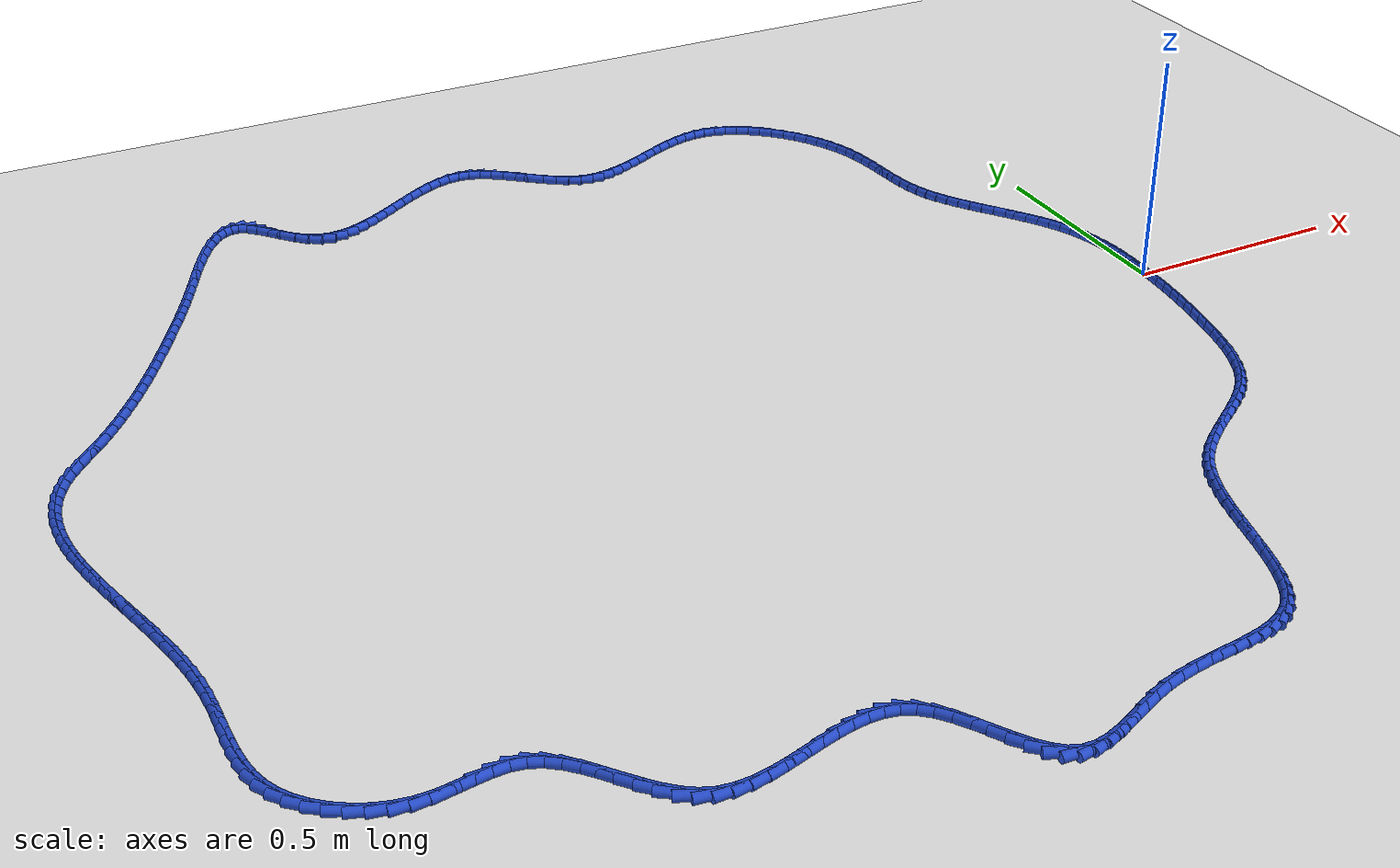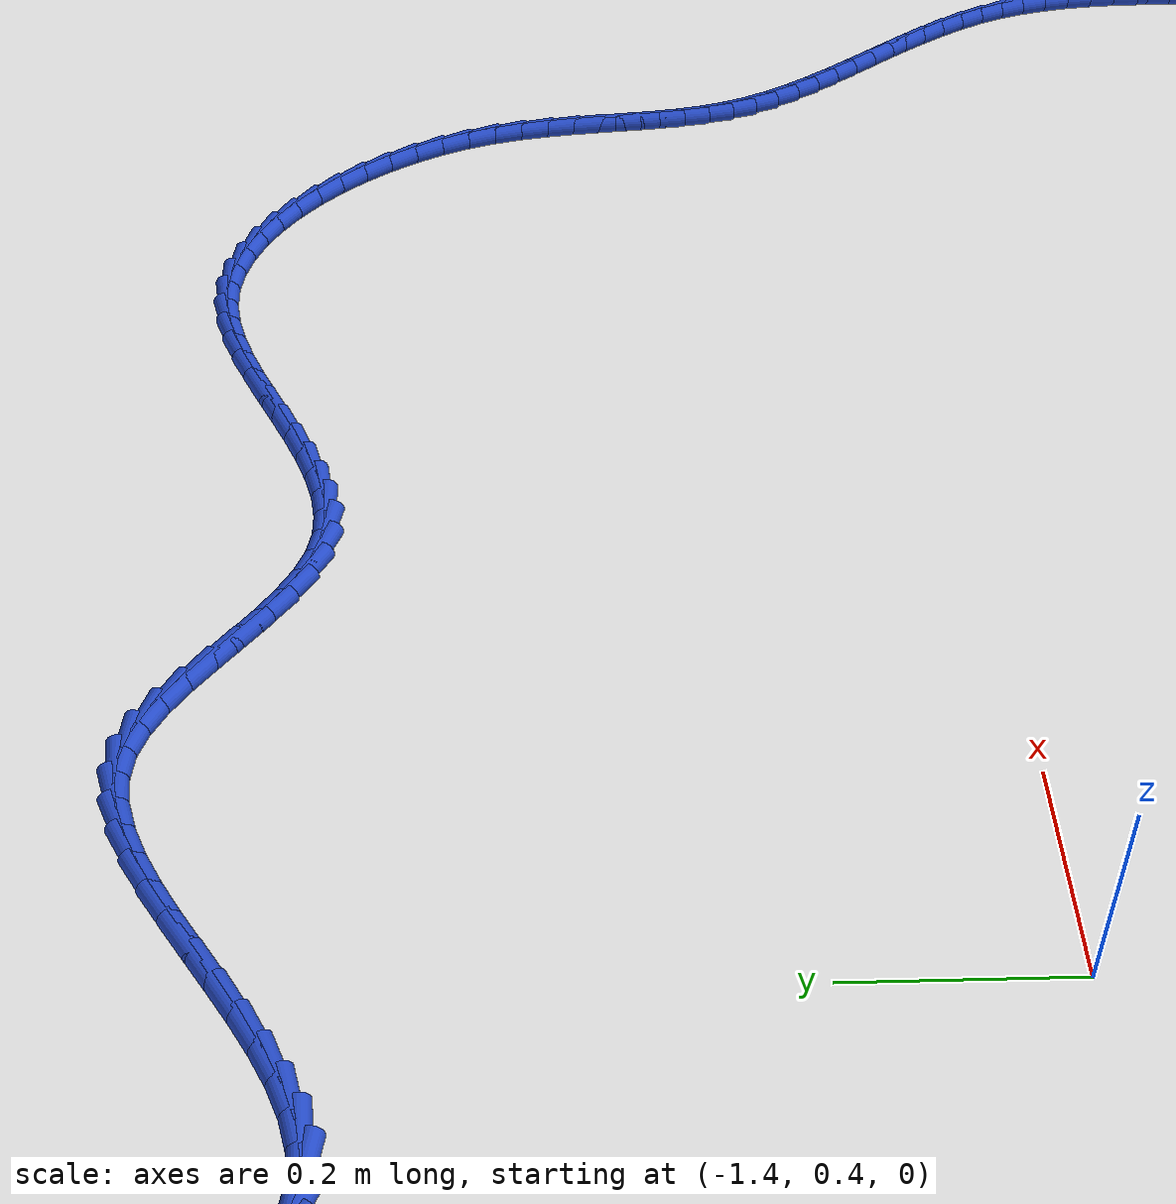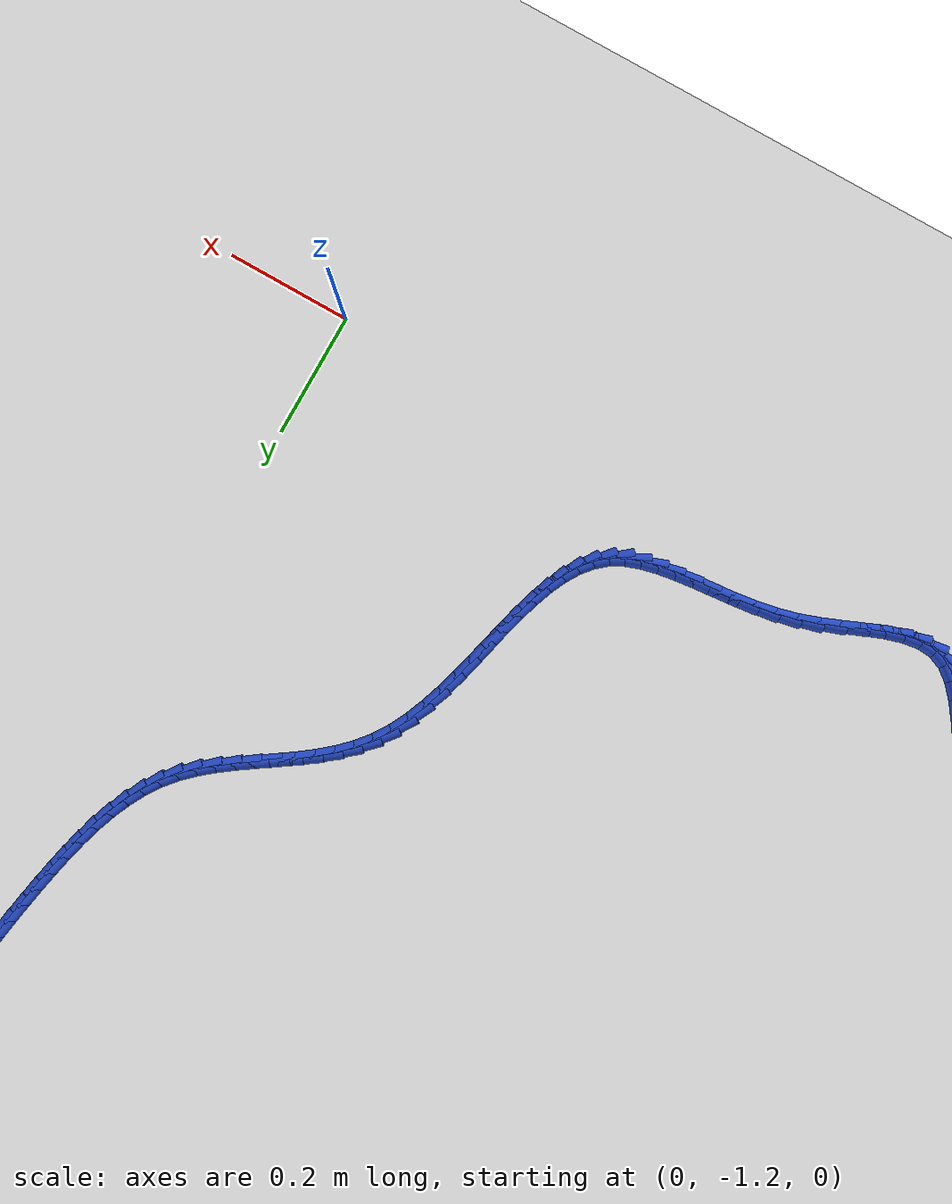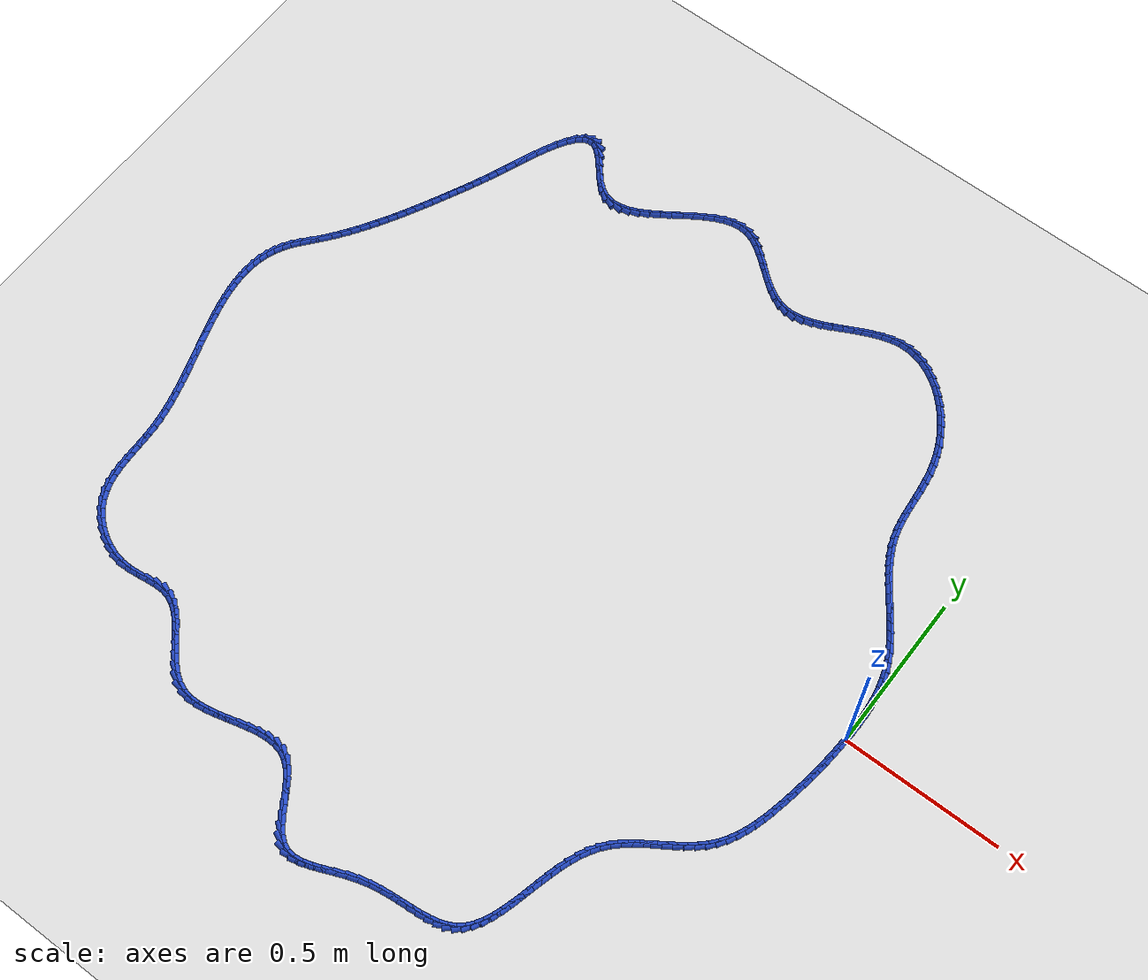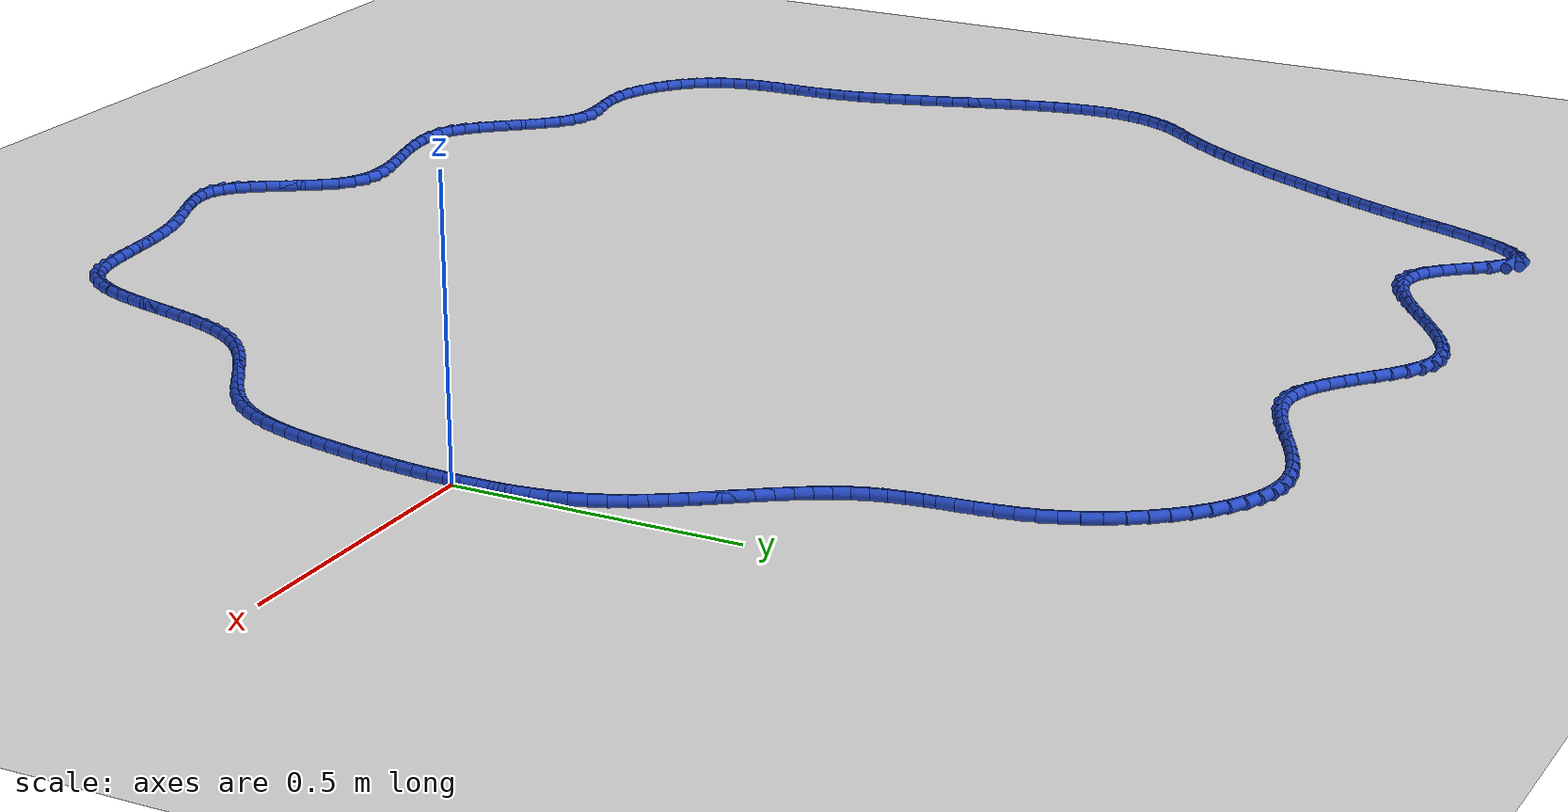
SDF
<sdf version="1.6">
 <world name="default">
  <light name="sun" type="directional">
   <pose>0 0 10 0 -0 0</pose>
   <diffuse>0.8 0.8 0.8 1</diffuse>
   <specular>0.2 0.2 0.2 1</specular>
   <attenuation>
    <range>1000</range>
    <constant>0.9</constant>
    <linear>0.01</linear>
    <quadratic>0.001</quadratic>
   </attenuation>
   <direction>-0.5 0.1 -0.9</direction>
  </light>
  <model name="ground_plane">
   <static>1</static>
   <link name="link">
    <collision name="collision">
     <geometry><plane><normal>0 0 1</normal><size>100 100</size></plane></geometry>
     <surface><friction><ode><mu>100</mu><mu2>50</mu2></ode></friction></surface>
    </collision>
    <visual name="visual">
     <cast_shadows>0</cast_shadows>
     <geometry><plane><normal>0 0 1</normal><size>100 100</size></plane></geometry>
     <material>
      <script><uri>file://media/materials/scripts/gazebo.material</uri><name>Gazebo/WhiteGlow</name></script>
     </material>
    </visual>
   </link>
  </model>
  <gravity>0 0 -9.8</gravity>
  <magnetic_field>6e-06 2.3e-05 -4.2e-05</magnetic_field>
  <atmosphere type="adiabatic"/>
  <physics name="default_physics" default="0" type="ode">
   <max_step_size>0.001</max_step_size>
   <real_time_factor>1</real_time_factor>
   <real_time_update_rate>1000</real_time_update_rate>
  </physics>
  <scene><ambient>0.4 0.4 0.4 1</ambient><background>0.7 0.7 0.7 1</background><shadows>1</shadows></scene>
  <spherical_coordinates>
   <surface_model>EARTH_WGS84</surface_model>
   <latitude_deg>0</latitude_deg>
   <longitude_deg>0</longitude_deg>
   <elevation>0</elevation>
   <heading_deg>0</heading_deg>
  </spherical_coordinates>
  <model name="line">
   <link name="link_0">
    <pose>8.239936510889834e-18 7.632783294297951e-17 0.01 0 1.57 1.5415442032016824</pose>
    <collision name="collision">
     <geometry><cylinder><radius>0.01</radius><length>0.08</length></cylinder></geometry>
    </collision>
    <visual name="visual">
     <material>
      <script><name>Gazebo/Blue</name><uri>file://media/materials/scripts/gazebo.material</uri></script>
     </material>
     <geometry><cylinder><radius>0.01</radius><length>0.08</length></cylinder></geometry>
    </visual>
   </link>
   <link name="link_1">
    <pose>0.0008711462181971203 0.029772119796999546 0.01 0 1.57 1.569325769403942</pose>
    <collision name="collision">
     <geometry><cylinder><radius>0.01</radius><length>0.08</length></cylinder></geometry>
    </collision>
    <visual name="visual">
     <material>
      <script><name>Gazebo/Blue</name><uri>file://media/materials/scripts/gazebo.material</uri></script>
     </material>
     <geometry><cylinder><radius>0.01</radius><length>0.08</length></cylinder></geometry>
    </visual>
   </link>
   <link name="link_2">
    <pose>0.0009151389869300071 0.0596878084273487 0.01 0 1.57 -1.537992764220976</pose>
    <collision name="collision">
     <geometry><cylinder><radius>0.01</radius><length>0.08</length></cylinder></geometry>
    </collision>
    <visual name="visual">
     <material>
      <script><name>Gazebo/Blue</name><uri>file://media/materials/scripts/gazebo.material</uri></script>
     </material>
     <geometry><cylinder><radius>0.01</radius><length>0.08</length></cylinder></geometry>
    </visual>
   </link>
   <link name="link_3">
    <pose>-6.68812110246541e-05 0.0896134583755524 0.01 0 1.57 -1.4968794196541226</pose>
    <collision name="collision">
     <geometry><cylinder><radius>0.01</radius><length>0.08</length></cylinder></geometry>
    </collision>
    <visual name="visual">
     <material>
      <script><name>Gazebo/Blue</name><uri>file://media/materials/scripts/gazebo.material</uri></script>
     </material>
     <geometry><cylinder><radius>0.01</radius><length>0.08</length></cylinder></geometry>
    </visual>
   </link>
   <link name="link_4">
    <pose>-0.0022737738928901895 0.11941546212611549 0.01 0 1.57 -1.448523730324683</pose>
    <collision name="collision">
     <geometry><cylinder><radius>0.01</radius><length>0.08</length></cylinder></geometry>
    </collision>
    <visual name="visual">
     <material>
      <script><name>Gazebo/Blue</name><uri>file://media/materials/scripts/gazebo.material</uri></script>
     </material>
     <geometry><cylinder><radius>0.01</radius><length>0.08</length></cylinder></geometry>
    </visual>
   </link>
   <link name="link_5">
    <pose>-0.005904398575889921 0.1489602121635429 0.01 0 1.57 -1.3925201223424315</pose>
    <collision name="collision">
     <geometry><cylinder><radius>0.01</radius><length>0.08</length></cylinder></geometry>
    </collision>
    <visual name="visual">
     <material>
      <script><name>Gazebo/Blue</name><uri>file://media/materials/scripts/gazebo.material</uri></script>
     </material>
     <geometry><cylinder><radius>0.01</radius><length>0.08</length></cylinder></geometry>
    </visual>
   </link>
   <link name="link_6">
    <pose>-0.011157614777247174 0.17811410097233937 0.01 0 1.57 -1.3285378208815364</pose>
    <collision name="collision">
     <geometry><cylinder><radius>0.01</radius><length>0.08</length></cylinder></geometry>
    </collision>
    <visual name="visual">
     <material>
      <script><name>Gazebo/Blue</name><uri>file://media/materials/scripts/gazebo.material</uri></script>
     </material>
     <geometry><cylinder><radius>0.01</radius><length>0.08</length></cylinder></geometry>
    </visual>
   </link>
   <link name="link_7">
    <pose>-0.018232282014185273 0.2067435210370099 0.01 0 1.57 -1.25642568086422</pose>
    <collision name="collision">
     <geometry><cylinder><radius>0.01</radius><length>0.08</length></cylinder></geometry>
    </collision>
    <visual name="visual">
     <material>
      <script><name>Gazebo/Blue</name><uri>file://media/materials/scripts/gazebo.material</uri></script>
     </material>
     <geometry><cylinder><radius>0.01</radius><length>0.08</length></cylinder></geometry>
    </visual>
   </link>
   <link name="link_8">
    <pose>-0.02732725980392754 0.23471486484205925 0.01 0 1.57 -1.178316283309899</pose>
    <collision name="collision">
     <geometry><cylinder><radius>0.01</radius><length>0.08</length></cylinder></geometry>
    </collision>
    <visual name="visual">
     <material>
      <script><name>Gazebo/Blue</name><uri>file://media/materials/scripts/gazebo.material</uri></script>
     </material>
     <geometry><cylinder><radius>0.01</radius><length>0.08</length></cylinder></geometry>
    </visual>
   </link>
   <link name="link_9">
    <pose>-0.03858830310602625 0.2619182802103138 0.01 0 1.57 -1.1078305133833755</pose>
    <collision name="collision">
     <geometry><cylinder><radius>0.01</radius><length>0.08</length></cylinder></geometry>
    </collision>
    <visual name="visual">
     <material>
      <script><name>Gazebo/Blue</name><uri>file://media/materials/scripts/gazebo.material</uri></script>
     </material>
     <geometry><cylinder><radius>0.01</radius><length>0.08</length></cylinder></geometry>
    </visual>
   </link>
   <link name="link_10">
    <pose>-0.051807631303384505 0.2884020625436457 0.01 0 1.57 -1.0505280170624138</pose>
    <collision name="collision">
     <geometry><cylinder><radius>0.01</radius><length>0.08</length></cylinder></geometry>
    </collision>
    <visual name="visual">
     <material>
      <script><name>Gazebo/Blue</name><uri>file://media/materials/scripts/gazebo.material</uri></script>
     </material>
     <geometry><cylinder><radius>0.01</radius><length>0.08</length></cylinder></geometry>
    </visual>
   </link>
   <link name="link_11">
    <pose>-0.06663305832135749 0.31427910434538053 0.01 0 1.57 -1.0061491479166482</pose>
    <collision name="collision">
     <geometry><cylinder><radius>0.01</radius><length>0.08</length></cylinder></geometry>
    </collision>
    <visual name="visual">
     <material>
      <script><name>Gazebo/Blue</name><uri>file://media/materials/scripts/gazebo.material</uri></script>
     </material>
     <geometry><cylinder><radius>0.01</radius><length>0.08</length></cylinder></geometry>
    </visual>
   </link>
   <link name="link_12">
    <pose>-0.08271196913370554 0.3396624900023791 0.01 0 1.57 -0.974225262000205</pose>
    <collision name="collision">
     <geometry><cylinder><radius>0.01</radius><length>0.08</length></cylinder></geometry>
    </collision>
    <visual name="visual">
     <material>
      <script><name>Gazebo/Blue</name><uri>file://media/materials/scripts/gazebo.material</uri></script>
     </material>
     <geometry><cylinder><radius>0.01</radius><length>0.08</length></cylinder></geometry>
    </visual>
   </link>
   <link name="link_13">
    <pose>-0.09969174871418904 0.36466530390150226 0.01 0 1.57 -0.9543062040659545</pose>
    <collision name="collision">
     <geometry><cylinder><radius>0.01</radius><length>0.08</length></cylinder></geometry>
    </collision>
    <visual name="visual">
     <material>
      <script><name>Gazebo/Blue</name><uri>file://media/materials/scripts/gazebo.material</uri></script>
     </material>
     <geometry><cylinder><radius>0.01</radius><length>0.08</length></cylinder></geometry>
    </visual>
   </link>
   <link name="link_14">
    <pose>-0.11721978203656837 0.3894006304296106 0.01 0 1.57 -0.946092884319966</pose>
    <collision name="collision">
     <geometry><cylinder><radius>0.01</radius><length>0.08</length></cylinder></geometry>
    </collision>
    <visual name="visual">
     <material>
      <script><name>Gazebo/Blue</name><uri>file://media/materials/scripts/gazebo.material</uri></script>
     </material>
     <geometry><cylinder><radius>0.01</radius><length>0.08</length></cylinder></geometry>
    </visual>
   </link>
   <link name="link_15">
    <pose>-0.1349434540746039 0.41398155397356495 0.01 0 1.57 -0.9495112700554809</pose>
    <collision name="collision">
     <geometry><cylinder><radius>0.01</radius><length>0.08</length></cylinder></geometry>
    </collision>
    <visual name="visual">
     <material>
      <script><name>Gazebo/Blue</name><uri>file://media/materials/scripts/gazebo.material</uri></script>
     </material>
     <geometry><cylinder><radius>0.01</radius><length>0.08</length></cylinder></geometry>
    </visual>
   </link>
   <link name="link_16">
    <pose>-0.15251014980205604 0.43852115892022625 0.01 0 1.57 -0.9647447153172607</pose>
    <collision name="collision">
     <geometry><cylinder><radius>0.01</radius><length>0.08</length></cylinder></geometry>
    </collision>
    <visual name="visual">
     <material>
      <script><name>Gazebo/Blue</name><uri>file://media/materials/scripts/gazebo.material</uri></script>
     </material>
     <geometry><cylinder><radius>0.01</radius><length>0.08</length></cylinder></geometry>
    </visual>
   </link>
   <link name="link_17">
    <pose>-0.16956725419268512 0.463132529656455 0.01 0 1.57 -0.9922311869009011</pose>
    <collision name="collision">
     <geometry><cylinder><radius>0.01</radius><length>0.08</length></cylinder></geometry>
    </collision>
    <visual name="visual">
     <material>
      <script><name>Gazebo/Blue</name><uri>file://media/materials/scripts/gazebo.material</uri></script>
     </material>
     <geometry><cylinder><radius>0.01</radius><length>0.08</length></cylinder></geometry>
    </visual>
   </link>
   <link name="link_18">
    <pose>-0.1857621522202515 0.487928750569112 0.01 0 1.57 -1.0326189504476706</pose>
    <collision name="collision">
     <geometry><cylinder><radius>0.01</radius><length>0.08</length></cylinder></geometry>
    </collision>
    <visual name="visual">
     <material>
      <script><name>Gazebo/Blue</name><uri>file://media/materials/scripts/gazebo.material</uri></script>
     </material>
     <geometry><cylinder><radius>0.01</radius><length>0.08</length></cylinder></geometry>
    </visual>
   </link>
   <link name="link_19">
    <pose>-0.20074222885851556 0.5130229060450582 0.01 0 1.57 -1.0866603592399513</pose>
    <collision name="collision">
     <geometry><cylinder><radius>0.01</radius><length>0.08</length></cylinder></geometry>
    </collision>
    <visual name="visual">
     <material>
      <script><name>Gazebo/Blue</name><uri>file://media/materials/scripts/gazebo.material</uri></script>
     </material>
     <geometry><cylinder><radius>0.01</radius><length>0.08</length></cylinder></geometry>
    </visual>
   </link>
   <link name="link_20">
    <pose>-0.2141548690812377 0.5385280804711542 0.01 0 1.57 -1.1550121401697506</pose>
    <collision name="collision">
     <geometry><cylinder><radius>0.01</radius><length>0.08</length></cylinder></geometry>
    </collision>
    <visual name="visual">
     <material>
      <script><name>Gazebo/Blue</name><uri>file://media/materials/scripts/gazebo.material</uri></script>
     </material>
     <geometry><cylinder><radius>0.01</radius><length>0.08</length></cylinder></geometry>
    </visual>
   </link>
   <link name="link_21">
    <pose>-0.22564745786217827 0.5645573582342607 0.01 0 1.57 -1.2377594350238477</pose>
    <collision name="collision">
     <geometry><cylinder><radius>0.01</radius><length>0.08</length></cylinder></geometry>
    </collision>
    <visual name="visual">
     <material>
      <script><name>Gazebo/Blue</name><uri>file://media/materials/scripts/gazebo.material</uri></script>
     </material>
     <geometry><cylinder><radius>0.01</radius><length>0.08</length></cylinder></geometry>
    </visual>
   </link>
   <link name="link_22">
    <pose>-0.2348716467486136 0.5912229057309557 0.01 0 1.57 -1.3230352621951371</pose>
    <collision name="collision">
     <geometry><cylinder><radius>0.01</radius><length>0.08</length></cylinder></geometry>
    </collision>
    <visual name="visual">
     <material>
      <script><name>Gazebo/Blue</name><uri>file://media/materials/scripts/gazebo.material</uri></script>
     </material>
     <geometry><cylinder><radius>0.01</radius><length>0.08</length></cylinder></geometry>
    </visual>
   </link>
   <link name="link_23">
    <pose>-0.24178935651056896 0.6185701322445123 0.01 0 1.57 -1.3908075151763792</pose>
    <collision name="collision">
     <geometry><cylinder><radius>0.01</radius><length>0.08</length></cylinder></geometry>
    </collision>
    <visual name="visual">
     <material>
      <script><name>Gazebo/Blue</name><uri>file://media/materials/scripts/gazebo.material</uri></script>
     </material>
     <geometry><cylinder><radius>0.01</radius><length>0.08</length></cylinder></geometry>
    </visual>
   </link>
   <link name="link_24">
    <pose>-0.2468775384871621 0.6465336337659556 0.01 0 1.57 -1.438809202886859</pose>
    <collision name="collision">
     <geometry><cylinder><radius>0.01</radius><length>0.08</length></cylinder></geometry>
    </collision>
    <visual name="visual">
     <material>
      <script><name>Gazebo/Blue</name><uri>file://media/materials/scripts/gazebo.material</uri></script>
     </material>
     <geometry><cylinder><radius>0.01</radius><length>0.08</length></cylinder></geometry>
    </visual>
   </link>
   <link name="link_25">
    <pose>-0.2506616895264971 0.6750375612991638 0.01 0 1.57 -1.4674116010361584</pose>
    <collision name="collision">
     <geometry><cylinder><radius>0.01</radius><length>0.08</length></cylinder></geometry>
    </collision>
    <visual name="visual">
     <material>
      <script><name>Gazebo/Blue</name><uri>file://media/materials/scripts/gazebo.material</uri></script>
     </material>
     <geometry><cylinder><radius>0.01</radius><length>0.08</length></cylinder></geometry>
    </visual>
   </link>
   <link name="link_26">
    <pose>-0.25366730647667785 0.7040060658480147 0.01 0 1.57 -1.477308093582962</pose>
    <collision name="collision">
     <geometry><cylinder><radius>0.01</radius><length>0.08</length></cylinder></geometry>
    </collision>
    <visual name="visual">
     <material>
      <script><name>Gazebo/Blue</name><uri>file://media/materials/scripts/gazebo.material</uri></script>
     </material>
     <geometry><cylinder><radius>0.01</radius><length>0.08</length></cylinder></geometry>
    </visual>
   </link>
   <link name="link_27">
    <pose>-0.2564198861858083 0.7333632984163864 0.01 0 1.57 -1.4691916375751166</pose>
    <collision name="collision">
     <geometry><cylinder><radius>0.01</radius><length>0.08</length></cylinder></geometry>
    </collision>
    <visual name="visual">
     <material>
      <script><name>Gazebo/Blue</name><uri>file://media/materials/scripts/gazebo.material</uri></script>
     </material>
     <geometry><cylinder><radius>0.01</radius><length>0.08</length></cylinder></geometry>
    </visual>
   </link>
   <link name="link_28">
    <pose>-0.2594449255019925 0.7630334100081567 0.01 0 1.57 -1.4436569713619698</pose>
    <collision name="collision">
     <geometry><cylinder><radius>0.01</radius><length>0.08</length></cylinder></geometry>
    </collision>
    <visual name="visual">
     <material>
      <script><name>Gazebo/Blue</name><uri>file://media/materials/scripts/gazebo.material</uri></script>
     </material>
     <geometry><cylinder><radius>0.01</radius><length>0.08</length></cylinder></geometry>
    </visual>
   </link>
   <link name="link_29">
    <pose>-0.26326792127333437 0.7929405516272037 0.01 0 1.57 -1.4012804235069265</pose>
    <collision name="collision">
     <geometry><cylinder><radius>0.01</radius><length>0.08</length></cylinder></geometry>
    </collision>
    <visual name="visual">
     <material>
      <script><name>Gazebo/Blue</name><uri>file://media/materials/scripts/gazebo.material</uri></script>
     </material>
     <geometry><cylinder><radius>0.01</radius><length>0.08</length></cylinder></geometry>
    </visual>
   </link>
   <link name="link_30">
    <pose>-0.26841437034793786 0.8230088742774052 0.01 0 1.57 -1.34283708026321</pose>
    <collision name="collision">
     <geometry><cylinder><radius>0.01</radius><length>0.08</length></cylinder></geometry>
    </collision>
    <visual name="visual">
     <material>
      <script><name>Gazebo/Blue</name><uri>file://media/materials/scripts/gazebo.material</uri></script>
     </material>
     <geometry><cylinder><radius>0.01</radius><length>0.08</length></cylinder></geometry>
    </visual>
   </link>
   <link name="link_31">
    <pose>-0.27540976957390695 0.8531625289626392 0.01 0 1.57 -1.26974281540994</pose>
    <collision name="collision">
     <geometry><cylinder><radius>0.01</radius><length>0.08</length></cylinder></geometry>
    </collision>
    <visual name="visual">
     <material>
      <script><name>Gazebo/Blue</name><uri>file://media/materials/scripts/gazebo.material</uri></script>
     </material>
     <geometry><cylinder><radius>0.01</radius><length>0.08</length></cylinder></geometry>
    </visual>
   </link>
   <link name="link_32">
    <pose>-0.2847745204758506 0.8833236366851134 0.01 0 1.57 -1.1906398646100351</pose>
    <collision name="collision">
     <geometry><cylinder><radius>0.01</radius><length>0.08</length></cylinder></geometry>
    </collision>
    <visual name="visual">
     <material>
      <script><name>Gazebo/Blue</name><uri>file://media/materials/scripts/gazebo.material</uri></script>
     </material>
     <geometry><cylinder><radius>0.01</radius><length>0.08</length></cylinder></geometry>
    </visual>
   </link>
   <link name="link_33">
    <pose>-0.2967549479770834 0.913305124995629 0.01 0 1.57 -1.1150935372289033</pose>
    <collision name="collision">
     <geometry><cylinder><radius>0.01</radius><length>0.08</length></cylinder></geometry>
    </collision>
    <visual name="visual">
     <material>
      <script><name>Gazebo/Blue</name><uri>file://media/materials/scripts/gazebo.material</uri></script>
     </material>
     <geometry><cylinder><radius>0.01</radius><length>0.08</length></cylinder></geometry>
    </visual>
   </link>
   <link name="link_34">
    <pose>-0.3111898179098793 0.9427575479202429 0.01 0 1.57 -1.0418199580308445</pose>
    <collision name="collision">
     <geometry><cylinder><radius>0.01</radius><length>0.08</length></cylinder></geometry>
    </collision>
    <visual name="visual">
     <material>
      <script><name>Gazebo/Blue</name><uri>file://media/materials/scripts/gazebo.material</uri></script>
     </material>
     <geometry><cylinder><radius>0.01</radius><length>0.08</length></cylinder></geometry>
    </visual>
   </link>
   <link name="link_35">
    <pose>-0.3278847797008966 0.9713182657478945 0.01 0 1.57 -0.9688181107099842</pose>
    <collision name="collision">
     <geometry><cylinder><radius>0.01</radius><length>0.08</length></cylinder></geometry>
    </collision>
    <visual name="visual">
     <material>
      <script><name>Gazebo/Blue</name><uri>file://media/materials/scripts/gazebo.material</uri></script>
     </material>
     <geometry><cylinder><radius>0.01</radius><length>0.08</length></cylinder></geometry>
    </visual>
   </link>
   <link name="link_36">
    <pose>-0.3466454827767934 0.9986246387675223 0.01 0 1.57 -0.8941456140368496</pose>
    <collision name="collision">
     <geometry><cylinder><radius>0.01</radius><length>0.08</length></cylinder></geometry>
    </collision>
    <visual name="visual">
     <material>
      <script><name>Gazebo/Blue</name><uri>file://media/materials/scripts/gazebo.material</uri></script>
     </material>
     <geometry><cylinder><radius>0.01</radius><length>0.08</length></cylinder></geometry>
    </visual>
   </link>
   <link name="link_37">
    <pose>-0.3672775765642281 1.024314027268066 0.01 0 1.57 -0.8158247522348239</pose>
    <collision name="collision">
     <geometry><cylinder><radius>0.01</radius><length>0.08</length></cylinder></geometry>
    </collision>
    <visual name="visual">
     <material>
      <script><name>Gazebo/Blue</name><uri>file://media/materials/scripts/gazebo.material</uri></script>
     </material>
     <geometry><cylinder><radius>0.01</radius><length>0.08</length></cylinder></geometry>
    </visual>
   </link>
   <link name="link_38">
    <pose>-0.3895867104898593 1.0480237915384656 0.01 0 1.57 -0.7317658666593437</pose>
    <collision name="collision">
     <geometry><cylinder><radius>0.01</radius><length>0.08</length></cylinder></geometry>
    </collision>
    <visual name="visual">
     <material>
      <script><name>Gazebo/Blue</name><uri>file://media/materials/scripts/gazebo.material</uri></script>
     </material>
     <geometry><cylinder><radius>0.01</radius><length>0.08</length></cylinder></geometry>
    </visual>
   </link>
   <link name="link_39">
    <pose>-0.41337853398034524 1.0693912918676598 0.01 0 1.57 -0.6397258939999189</pose>
    <collision name="collision">
     <geometry><cylinder><radius>0.01</radius><length>0.08</length></cylinder></geometry>
    </collision>
    <visual name="visual">
     <material>
      <script><name>Gazebo/Blue</name><uri>file://media/materials/scripts/gazebo.material</uri></script>
     </material>
     <geometry><cylinder><radius>0.01</radius><length>0.08</length></cylinder></geometry>
    </visual>
   </link>
   <link name="link_40">
    <pose>-0.43845869646234376 1.0880538885445878 0.01 0 1.57 -0.5373394767097778</pose>
    <collision name="collision">
     <geometry><cylinder><radius>0.01</radius><length>0.08</length></cylinder></geometry>
    </collision>
    <visual name="visual">
     <material>
      <script><name>Gazebo/Blue</name><uri>file://media/materials/scripts/gazebo.material</uri></script>
     </material>
     <geometry><cylinder><radius>0.01</radius><length>0.08</length></cylinder></geometry>
    </visual>
   </link>
   <link name="link_41">
    <pose>-0.46463284736251376 1.1036489418581898 0.01 0 1.57 -0.422290613328357</pose>
    <collision name="collision">
     <geometry><cylinder><radius>0.01</radius><length>0.08</length></cylinder></geometry>
    </collision>
    <visual name="visual">
     <material>
      <script><name>Gazebo/Blue</name><uri>file://media/materials/scripts/gazebo.material</uri></script>
     </material>
     <geometry><cylinder><radius>0.01</radius><length>0.08</length></cylinder></geometry>
    </visual>
   </link>
   <link name="link_42">
    <pose>-0.4917066361075134 1.1158138120974044 0.01 0 1.57 -0.29272202244233986</pose>
    <collision name="collision">
     <geometry><cylinder><radius>0.01</radius><length>0.08</length></cylinder></geometry>
    </collision>
    <visual name="visual">
     <material>
      <script><name>Gazebo/Blue</name><uri>file://media/materials/scripts/gazebo.material</uri></script>
     </material>
     <geometry><cylinder><radius>0.01</radius><length>0.08</length></cylinder></geometry>
    </visual>
   </link>
   <link name="link_43">
    <pose>-0.5194857121240012 1.1241858595511716 0.01 0 1.57 -0.14795929010274467</pose>
    <collision name="collision">
     <geometry><cylinder><radius>0.01</radius><length>0.08</length></cylinder></geometry>
    </collision>
    <visual name="visual">
     <material>
      <script><name>Gazebo/Blue</name><uri>file://media/materials/scripts/gazebo.material</uri></script>
     </material>
     <geometry><cylinder><radius>0.01</radius><length>0.08</length></cylinder></geometry>
    </visual>
   </link>
   <link name="link_44">
    <pose>-0.5477757248386348 1.12840244450843 0.01 0 1.57 0.010063030693174177</pose>
    <collision name="collision">
     <geometry><cylinder><radius>0.01</radius><length>0.08</length></cylinder></geometry>
    </collision>
    <visual name="visual">
     <material>
      <script><name>Gazebo/Blue</name><uri>file://media/materials/scripts/gazebo.material</uri></script>
     </material>
     <geometry><cylinder><radius>0.01</radius><length>0.08</length></cylinder></geometry>
    </visual>
   </link>
   <link name="link_45">
    <pose>-0.5763838578656565 1.1281145502698087 0.01 0 1.57 0.15999588747395185</pose>
    <collision name="collision">
     <geometry><cylinder><radius>0.01</radius><length>0.08</length></cylinder></geometry>
    </collision>
    <visual name="visual">
     <material>
      <script><name>Gazebo/Blue</name><uri>file://media/materials/scripts/gazebo.material</uri></script>
     </material>
     <geometry><cylinder><radius>0.01</radius><length>0.08</length></cylinder></geometry>
    </visual>
   </link>
   <link name="link_46">
    <pose>-0.6051730989071227 1.1234686795554232 0.01 0 1.57 0.2774837882327957</pose>
    <collision name="collision">
     <geometry><cylinder><radius>0.01</radius><length>0.08</length></cylinder></geometry>
    </collision>
    <visual name="visual">
     <material>
      <script><name>Gazebo/Blue</name><uri>file://media/materials/scripts/gazebo.material</uri></script>
     </material>
     <geometry><cylinder><radius>0.01</radius><length>0.08</length></cylinder></geometry>
    </visual>
   </link>
   <link name="link_47">
    <pose>-0.6340767821019241 1.1152359851228304 0.01 0 1.57 0.36330452308582345</pose>
    <collision name="collision">
     <geometry><cylinder><radius>0.01</radius><length>0.08</length></cylinder></geometry>
    </collision>
    <visual name="visual">
     <material>
      <script><name>Gazebo/Blue</name><uri>file://media/materials/scripts/gazebo.material</uri></script>
     </material>
     <geometry><cylinder><radius>0.01</radius><length>0.08</length></cylinder></geometry>
    </visual>
   </link>
   <link name="link_48">
    <pose>-0.6630327332318705 1.1042275038380627 0.01 0 1.57 0.4213449314231461</pose>
    <collision name="collision">
     <geometry><cylinder><radius>0.01</radius><length>0.08</length></cylinder></geometry>
    </collision>
    <visual name="visual">
     <material>
      <script><name>Gazebo/Blue</name><uri>file://media/materials/scripts/gazebo.material</uri></script>
     </material>
     <geometry><cylinder><radius>0.01</radius><length>0.08</length></cylinder></geometry>
    </visual>
   </link>
   <link name="link_49">
    <pose>-0.691978778078772 1.0912542725671512 0.01 0 1.57 0.45502066951421105</pose>
    <collision name="collision">
     <geometry><cylinder><radius>0.01</radius><length>0.08</length></cylinder></geometry>
    </collision>
    <visual name="visual">
     <material>
      <script><name>Gazebo/Blue</name><uri>file://media/materials/scripts/gazebo.material</uri></script>
     </material>
     <geometry><cylinder><radius>0.01</radius><length>0.08</length></cylinder></geometry>
    </visual>
   </link>
   <link name="link_50">
    <pose>-0.7208527424244382 1.0771273281761264 0.01 0 1.57 0.4664208378407781</pose>
    <collision name="collision">
     <geometry><cylinder><radius>0.01</radius><length>0.08</length></cylinder></geometry>
    </collision>
    <visual name="visual">
     <material>
      <script><name>Gazebo/Blue</name><uri>file://media/materials/scripts/gazebo.material</uri></script>
     </material>
     <geometry><cylinder><radius>0.01</radius><length>0.08</length></cylinder></geometry>
    </visual>
   </link>
   <link name="link_51">
    <pose>-0.7495924520506789 1.0626577075310202 0.01 0 1.57 0.4560408181119525</pose>
    <collision name="collision">
     <geometry><cylinder><radius>0.01</radius><length>0.08</length></cylinder></geometry>
    </collision>
    <visual name="visual">
     <material>
      <script><name>Gazebo/Blue</name><uri>file://media/materials/scripts/gazebo.material</uri></script>
     </material>
     <geometry><cylinder><radius>0.01</radius><length>0.08</length></cylinder></geometry>
    </visual>
   </link>
   <link name="link_52">
    <pose>-0.7781357327393037 1.048656447497864 0.01 0 1.57 0.42267037942850205</pose>
    <collision name="collision">
     <geometry><cylinder><radius>0.01</radius><length>0.08</length></cylinder></geometry>
    </collision>
    <visual name="visual">
     <material>
      <script><name>Gazebo/Blue</name><uri>file://media/materials/scripts/gazebo.material</uri></script>
     </material>
     <geometry><cylinder><radius>0.01</radius><length>0.08</length></cylinder></geometry>
    </visual>
   </link>
   <link name="link_53">
    <pose>-0.8064204102721225 1.0359345849426886 0.01 0 1.57 0.363307807847391</pose>
    <collision name="collision">
     <geometry><cylinder><radius>0.01</radius><length>0.08</length></cylinder></geometry>
    </collision>
    <visual name="visual">
     <material>
      <script><name>Gazebo/Blue</name><uri>file://media/materials/scripts/gazebo.material</uri></script>
     </material>
     <geometry><cylinder><radius>0.01</radius><length>0.08</length></cylinder></geometry>
    </visual>
   </link>
   <link name="link_54">
    <pose>-0.8343843104309454 1.0253031567315258 0.01 0 1.57 0.2732538306652313</pose>
    <collision name="collision">
     <geometry><cylinder><radius>0.01</radius><length>0.08</length></cylinder></geometry>
    </collision>
    <visual name="visual">
     <material>
      <script><name>Gazebo/Blue</name><uri>file://media/materials/scripts/gazebo.material</uri></script>
     </material>
     <geometry><cylinder><radius>0.01</radius><length>0.08</length></cylinder></geometry>
    </visual>
   </link>
   <link name="link_55">
    <pose>-0.8619652589975817 1.0175731997304065 0.01 0 1.57 0.1469819663390464</pose>
    <collision name="collision">
     <geometry><cylinder><radius>0.01</radius><length>0.08</length></cylinder></geometry>
    </collision>
    <visual name="visual">
     <material>
      <script><name>Gazebo/Blue</name><uri>file://media/materials/scripts/gazebo.material</uri></script>
     </material>
     <geometry><cylinder><radius>0.01</radius><length>0.08</length></cylinder></geometry>
    </visual>
   </link>
   <link name="link_56">
    <pose>-0.8891010817538416 1.0135557508053623 0.01 0 1.57 -0.01900349854624457</pose>
    <collision name="collision">
     <geometry><cylinder><radius>0.01</radius><length>0.08</length></cylinder></geometry>
    </collision>
    <visual name="visual">
     <material>
      <script><name>Gazebo/Blue</name><uri>file://media/materials/scripts/gazebo.material</uri></script>
     </material>
     <geometry><cylinder><radius>0.01</radius><length>0.08</length></cylinder></geometry>
    </visual>
   </link>
   <link name="link_57">
    <pose>-0.9157296044815342 1.0140618468224238 0.01 0 1.57 -0.2191437274482809</pose>
    <collision name="collision">
     <geometry><cylinder><radius>0.01</radius><length>0.08</length></cylinder></geometry>
    </collision>
    <visual name="visual">
     <material>
      <script><name>Gazebo/Blue</name><uri>file://media/materials/scripts/gazebo.material</uri></script>
     </material>
     <geometry><cylinder><radius>0.01</radius><length>0.08</length></cylinder></geometry>
    </visual>
   </link>
   <link name="link_58">
    <pose>-0.941792147345468 1.0198665094631543 0.01 0 1.57 -0.4059484354433069</pose>
    <collision name="collision">
     <geometry><cylinder><radius>0.01</radius><length>0.08</length></cylinder></geometry>
    </collision>
    <visual name="visual">
     <material>
      <script><name>Gazebo/Blue</name><uri>file://media/materials/scripts/gazebo.material</uri></script>
     </material>
     <geometry><cylinder><radius>0.01</radius><length>0.08</length></cylinder></geometry>
    </visual>
   </link>
   <link name="link_59">
    <pose>-0.9673179994123623 1.0308381007120917 0.01 0 1.57 -0.5400663090289796</pose>
    <collision name="collision">
     <geometry><cylinder><radius>0.01</radius><length>0.08</length></cylinder></geometry>
    </collision>
    <visual name="visual">
     <material>
      <script><name>Gazebo/Blue</name><uri>file://media/materials/scripts/gazebo.material</uri></script>
     </material>
     <geometry><cylinder><radius>0.01</radius><length>0.08</length></cylinder></geometry>
    </visual>
   </link>
   <link name="link_60">
    <pose>-0.9924288590657139 1.0458925573065727 0.01 0 1.57 -0.6276295036116257</pose>
    <collision name="collision">
     <geometry><cylinder><radius>0.01</radius><length>0.08</length></cylinder></geometry>
    </collision>
    <visual name="visual">
     <material>
      <script><name>Gazebo/Blue</name><uri>file://media/materials/scripts/gazebo.material</uri></script>
     </material>
     <geometry><cylinder><radius>0.01</radius><length>0.08</length></cylinder></geometry>
    </visual>
   </link>
   <link name="link_61">
    <pose>-1.0172508078301612 1.0639006407307046 0.01 0 1.57 -0.6773362717830139</pose>
    <collision name="collision">
     <geometry><cylinder><radius>0.01</radius><length>0.08</length></cylinder></geometry>
    </collision>
    <visual name="visual">
     <material>
      <script><name>Gazebo/Blue</name><uri>file://media/materials/scripts/gazebo.material</uri></script>
     </material>
     <geometry><cylinder><radius>0.01</radius><length>0.08</length></cylinder></geometry>
    </visual>
   </link>
   <link name="link_62">
    <pose>-1.0419099272303436 1.0837331124685974 0.01 0 1.57 -0.6947757357571528</pose>
    <collision name="collision">
     <geometry><cylinder><radius>0.01</radius><length>0.08</length></cylinder></geometry>
    </collision>
    <visual name="visual">
     <material>
      <script><name>Gazebo/Blue</name><uri>file://media/materials/scripts/gazebo.material</uri></script>
     </material>
     <geometry><cylinder><radius>0.01</radius><length>0.08</length></cylinder></geometry>
    </visual>
   </link>
   <link name="link_63">
    <pose>-1.0665329073555323 1.104253825519677 0.01 0 1.57 -0.6780584342296228</pose>
    <collision name="collision">
     <geometry><cylinder><radius>0.01</radius><length>0.08</length></cylinder></geometry>
    </collision>
    <visual name="visual">
     <material>
      <script><name>Gazebo/Blue</name><uri>file://media/materials/scripts/gazebo.material</uri></script>
     </material>
     <geometry><cylinder><radius>0.01</radius><length>0.08</length></cylinder></geometry>
    </visual>
   </link>
   <link name="link_64">
    <pose>-1.0912601882447839 1.1241705421211128 0.01 0 1.57 -0.620754193370026</pose>
    <collision name="collision">
     <geometry><cylinder><radius>0.01</radius><length>0.08</length></cylinder></geometry>
    </collision>
    <visual name="visual">
     <material>
      <script><name>Gazebo/Blue</name><uri>file://media/materials/scripts/gazebo.material</uri></script>
     </material>
     <geometry><cylinder><radius>0.01</radius><length>0.08</length></cylinder></geometry>
    </visual>
   </link>
   <link name="link_65">
    <pose>-1.1162458240286837 1.142036476023913 0.01 0 1.57 -0.5146309187651498</pose>
    <collision name="collision">
     <geometry><cylinder><radius>0.01</radius><length>0.08</length></cylinder></geometry>
    </collision>
    <visual name="visual">
     <material>
      <script><name>Gazebo/Blue</name><uri>file://media/materials/scripts/gazebo.material</uri></script>
     </material>
     <geometry><cylinder><radius>0.01</radius><length>0.08</length></cylinder></geometry>
    </visual>
   </link>
   <link name="link_66">
    <pose>-1.1416444502299576 1.1563982409591573 0.01 0 1.57 -0.34747569862418815</pose>
    <collision name="collision">
     <geometry><cylinder><radius>0.01</radius><length>0.08</length></cylinder></geometry>
    </collision>
    <visual name="visual">
     <material>
      <script><name>Gazebo/Blue</name><uri>file://media/materials/scripts/gazebo.material</uri></script>
     </material>
     <geometry><cylinder><radius>0.01</radius><length>0.08</length></cylinder></geometry>
    </visual>
   </link>
   <link name="link_67">
    <pose>-1.1676107023713325 1.1658024506579252 0.01 0 1.57 -0.11620844488841818</pose>
    <collision name="collision">
     <geometry><cylinder><radius>0.01</radius><length>0.08</length></cylinder></geometry>
    </collision>
    <visual name="visual">
     <material>
      <script><name>Gazebo/Blue</name><uri>file://media/materials/scripts/gazebo.material</uri></script>
     </material>
     <geometry><cylinder><radius>0.01</radius><length>0.08</length></cylinder></geometry>
    </visual>
   </link>
   <link name="link_68">
    <pose>-1.194285570228508 1.1689163252101482 0.01 0 1.57 0.1132284712387262</pose>
    <collision name="collision">
     <geometry><cylinder><radius>0.01</radius><length>0.08</length></cylinder></geometry>
    </collision>
    <visual name="visual">
     <material>
      <script><name>Gazebo/Blue</name><uri>file://media/materials/scripts/gazebo.material</uri></script>
     </material>
     <geometry><cylinder><radius>0.01</radius><length>0.08</length></cylinder></geometry>
    </visual>
   </link>
   <link name="link_69">
    <pose>-1.221651951743687 1.165804361114755 0.01 0 1.57 0.2912066357050443</pose>
    <collision name="collision">
     <geometry><cylinder><radius>0.01</radius><length>0.08</length></cylinder></geometry>
    </collision>
    <visual name="visual">
     <material>
      <script><name>Gazebo/Blue</name><uri>file://media/materials/scripts/gazebo.material</uri></script>
     </material>
     <geometry><cylinder><radius>0.01</radius><length>0.08</length></cylinder></geometry>
    </visual>
   </link>
   <link name="link_70">
    <pose>-1.249591005945047 1.157430262510288 0.01 0 1.57 0.419380567588263</pose>
    <collision name="collision">
     <geometry><cylinder><radius>0.01</radius><length>0.08</length></cylinder></geometry>
    </collision>
    <visual name="visual">
     <material>
      <script><name>Gazebo/Blue</name><uri>file://media/materials/scripts/gazebo.material</uri></script>
     </material>
     <geometry><cylinder><radius>0.01</radius><length>0.08</length></cylinder></geometry>
    </visual>
   </link>
   <link name="link_71">
    <pose>-1.2779822076684817 1.144772619074259 0.01 0 1.57 0.5072441272788148</pose>
    <collision name="collision">
     <geometry><cylinder><radius>0.01</radius><length>0.08</length></cylinder></geometry>
    </collision>
    <visual name="visual">
     <material>
      <script><name>Gazebo/Blue</name><uri>file://media/materials/scripts/gazebo.material</uri></script>
     </material>
     <geometry><cylinder><radius>0.01</radius><length>0.08</length></cylinder></geometry>
    </visual>
   </link>
   <link name="link_72">
    <pose>-1.3067050317498823 1.1288100204841793 0.01 0 1.57 0.5636845109770585</pose>
    <collision name="collision">
     <geometry><cylinder><radius>0.01</radius><length>0.08</length></cylinder></geometry>
    </collision>
    <visual name="visual">
     <material>
      <script><name>Gazebo/Blue</name><uri>file://media/materials/scripts/gazebo.material</uri></script>
     </material>
     <geometry><cylinder><radius>0.01</radius><length>0.08</length></cylinder></geometry>
    </visual>
   </link>
   <link name="link_73">
    <pose>-1.3356389530251436 1.1105210564175605 0.01 0 1.57 0.594818910414515</pose>
    <collision name="collision">
     <geometry><cylinder><radius>0.01</radius><length>0.08</length></cylinder></geometry>
    </collision>
    <visual name="visual">
     <material>
      <script><name>Gazebo/Blue</name><uri>file://media/materials/scripts/gazebo.material</uri></script>
     </material>
     <geometry><cylinder><radius>0.01</radius><length>0.08</length></cylinder></geometry>
    </visual>
   </link>
   <link name="link_74">
    <pose>-1.3646634463301586 1.0908843165519138 0.01 0 1.57 0.6039758114208391</pose>
    <collision name="collision">
     <geometry><cylinder><radius>0.01</radius><length>0.08</length></cylinder></geometry>
    </collision>
    <visual name="visual">
     <material>
      <script><name>Gazebo/Blue</name><uri>file://media/materials/scripts/gazebo.material</uri></script>
     </material>
     <geometry><cylinder><radius>0.01</radius><length>0.08</length></cylinder></geometry>
    </visual>
   </link>
   <link name="link_75">
    <pose>-1.3936579865008187 1.0708783905647496 0.01 0 1.57 0.5920037202527177</pose>
    <collision name="collision">
     <geometry><cylinder><radius>0.01</radius><length>0.08</length></cylinder></geometry>
    </collision>
    <visual name="visual">
     <material>
      <script><name>Gazebo/Blue</name><uri>file://media/materials/scripts/gazebo.material</uri></script>
     </material>
     <geometry><cylinder><radius>0.01</radius><length>0.08</length></cylinder></geometry>
    </visual>
   </link>
   <link name="link_76">
    <pose>-1.4225020483730182 1.0514818681335807 0.01 0 1.57 0.5573492386233017</pose>
    <collision name="collision">
     <geometry><cylinder><radius>0.01</radius><length>0.08</length></cylinder></geometry>
    </collision>
    <visual name="visual">
     <material>
      <script><name>Gazebo/Blue</name><uri>file://media/materials/scripts/gazebo.material</uri></script>
     </material>
     <geometry><cylinder><radius>0.01</radius><length>0.08</length></cylinder></geometry>
    </visual>
   </link>
   <link name="link_77">
    <pose>-1.4510751067826488 1.033673338935917 0.01 0 1.57 0.4957901919988571</pose>
    <collision name="collision">
     <geometry><cylinder><radius>0.01</radius><length>0.08</length></cylinder></geometry>
    </collision>
    <visual name="visual">
     <material>
      <script><name>Gazebo/Blue</name><uri>file://media/materials/scripts/gazebo.material</uri></script>
     </material>
     <geometry><cylinder><radius>0.01</radius><length>0.08</length></cylinder></geometry>
    </visual>
   </link>
   <link name="link_78">
    <pose>-1.479256636565605 1.0184313926492707 0.01 0 1.57 0.3999480874389885</pose>
    <collision name="collision">
     <geometry><cylinder><radius>0.01</radius><length>0.08</length></cylinder></geometry>
    </collision>
    <visual name="visual">
     <material>
      <script><name>Gazebo/Blue</name><uri>file://media/materials/scripts/gazebo.material</uri></script>
     </material>
     <geometry><cylinder><radius>0.01</radius><length>0.08</length></cylinder></geometry>
    </visual>
   </link>
   <link name="link_79">
    <pose>-1.5069261125577786 1.0067346189511532 0.01 0 1.57 0.2593302625753998</pose>
    <collision name="collision">
     <geometry><cylinder><radius>0.01</radius><length>0.08</length></cylinder></geometry>
    </collision>
    <visual name="visual">
     <material>
      <script><name>Gazebo/Blue</name><uri>file://media/materials/scripts/gazebo.material</uri></script>
     </material>
     <geometry><cylinder><radius>0.01</radius><length>0.08</length></cylinder></geometry>
    </visual>
   </link>
   <link name="link_80">
    <pose>-1.533963009595063 0.9995616075190752 0.01 0 1.57 0.06347695003753862</pose>
    <collision name="collision">
     <geometry><cylinder><radius>0.01</radius><length>0.08</length></cylinder></geometry>
    </collision>
    <visual name="visual">
     <material>
      <script><name>Gazebo/Blue</name><uri>file://media/materials/scripts/gazebo.material</uri></script>
     </material>
     <geometry><cylinder><radius>0.01</radius><length>0.08</length></cylinder></geometry>
    </visual>
   </link>
   <link name="link_81">
    <pose>-1.5602468025133507 0.9978909480305482 0.01 0 1.57 -0.18709149837114783</pose>
    <collision name="collision">
     <geometry><cylinder><radius>0.01</radius><length>0.08</length></cylinder></geometry>
    </collision>
    <visual name="visual">
     <material>
      <script><name>Gazebo/Blue</name><uri>file://media/materials/scripts/gazebo.material</uri></script>
     </material>
     <geometry><cylinder><radius>0.01</radius><length>0.08</length></cylinder></geometry>
    </visual>
   </link>
   <link name="link_82">
    <pose>-1.5856569661485351 1.0027012301630835 0.01 0 1.57 -0.46541060011991486</pose>
    <collision name="collision">
     <geometry><cylinder><radius>0.01</radius><length>0.08</length></cylinder></geometry>
    </collision>
    <visual name="visual">
     <material>
      <script><name>Gazebo/Blue</name><uri>file://media/materials/scripts/gazebo.material</uri></script>
     </material>
     <geometry><cylinder><radius>0.01</radius><length>0.08</length></cylinder></geometry>
    </visual>
   </link>
   <link name="link_83">
    <pose>-1.6100733873856257 1.0149632957275725 0.01 0 1.57 -0.6945155006325218</pose>
    <collision name="collision">
     <geometry><cylinder><radius>0.01</radius><length>0.08</length></cylinder></geometry>
    </collision>
    <visual name="visual">
     <material>
      <script><name>Gazebo/Blue</name><uri>file://media/materials/scripts/gazebo.material</uri></script>
     </material>
     <geometry><cylinder><radius>0.01</radius><length>0.08</length></cylinder></geometry>
    </visual>
   </link>
   <link name="link_84">
    <pose>-1.633440867891998 1.0344273770110093 0.01 0 1.57 -0.8173119481413946</pose>
    <collision name="collision">
     <geometry><cylinder><radius>0.01</radius><length>0.08</length></cylinder></geometry>
    </collision>
    <visual name="visual">
     <material>
      <script><name>Gazebo/Blue</name><uri>file://media/materials/scripts/gazebo.material</uri></script>
     </material>
     <geometry><cylinder><radius>0.01</radius><length>0.08</length></cylinder></geometry>
    </visual>
   </link>
   <link name="link_85">
    <pose>-1.6558393235288873 1.058303118997737 0.01 0 1.57 -0.8634671493344086</pose>
    <collision name="collision">
     <geometry><cylinder><radius>0.01</radius><length>0.08</length></cylinder></geometry>
    </collision>
    <visual name="visual">
     <material>
      <script><name>Gazebo/Blue</name><uri>file://media/materials/scripts/gazebo.material</uri></script>
     </material>
     <geometry><cylinder><radius>0.01</radius><length>0.08</length></cylinder></geometry>
    </visual>
   </link>
   <link name="link_86">
    <pose>-1.6773655347235532 1.0834830578541 0.01 0 1.57 -0.8448358490047891</pose>
    <collision name="collision">
     <geometry><cylinder><radius>0.01</radius><length>0.08</length></cylinder></geometry>
    </collision>
    <visual name="visual">
     <material>
      <script><name>Gazebo/Blue</name><uri>file://media/materials/scripts/gazebo.material</uri></script>
     </material>
     <geometry><cylinder><radius>0.01</radius><length>0.08</length></cylinder></geometry>
    </visual>
   </link>
   <link name="link_87">
    <pose>-1.6981162819032556 1.1068597297464418 0.01 0 1.57 -0.7437459403987068</pose>
    <collision name="collision">
     <geometry><cylinder><radius>0.01</radius><length>0.08</length></cylinder></geometry>
    </collision>
    <visual name="visual">
     <material>
      <script><name>Gazebo/Blue</name><uri>file://media/materials/scripts/gazebo.material</uri></script>
     </material>
     <geometry><cylinder><radius>0.01</radius><length>0.08</length></cylinder></geometry>
    </visual>
   </link>
   <link name="link_88">
    <pose>-1.7181883454952542 1.1253256708411066 0.01 0 1.57 -0.49218034463802124</pose>
    <collision name="collision">
     <geometry><cylinder><radius>0.01</radius><length>0.08</length></cylinder></geometry>
    </collision>
    <visual name="visual">
     <material>
      <script><name>Gazebo/Blue</name><uri>file://media/materials/scripts/gazebo.material</uri></script>
     </material>
     <geometry><cylinder><radius>0.01</radius><length>0.08</length></cylinder></geometry>
    </visual>
   </link>
   <link name="link_89">
    <pose>-1.7376784356611237 1.1357761026511883 0.01 0 1.57 -0.02379140664681015</pose>
    <collision name="collision">
     <geometry><cylinder><radius>0.01</radius><length>0.08</length></cylinder></geometry>
    </collision>
    <visual name="visual">
     <material>
      <script><name>Gazebo/Blue</name><uri>file://media/materials/scripts/gazebo.material</uri></script>
     </material>
     <geometry><cylinder><radius>0.01</radius><length>0.08</length></cylinder></geometry>
    </visual>
   </link>
   <link name="link_90">
    <pose>-1.7566539197736541 1.1362276413082084 0.01 0 1.57 0.4396517719784026</pose>
    <collision name="collision">
     <geometry><cylinder><radius>0.01</radius><length>0.08</length></cylinder></geometry>
    </collision>
    <visual name="visual">
     <material>
      <script><name>Gazebo/Blue</name><uri>file://media/materials/scripts/gazebo.material</uri></script>
     </material>
     <geometry><cylinder><radius>0.01</radius><length>0.08</length></cylinder></geometry>
    </visual>
   </link>
   <link name="link_91">
    <pose>-1.7751075657602657 1.127547873149653 0.01 0 1.57 0.744276896580897</pose>
    <collision name="collision">
     <geometry><cylinder><radius>0.01</radius><length>0.08</length></cylinder></geometry>
    </collision>
    <visual name="visual">
     <material>
      <script><name>Gazebo/Blue</name><uri>file://media/materials/scripts/gazebo.material</uri></script>
     </material>
     <geometry><cylinder><radius>0.01</radius><length>0.08</length></cylinder></geometry>
    </visual>
   </link>
   <link name="link_92">
    <pose>-1.7930204615725192 1.11105075865169 0.01 0 1.57 0.9244392739908857</pose>
    <collision name="collision">
     <geometry><cylinder><radius>0.01</radius><length>0.08</length></cylinder></geometry>
    </collision>
    <visual name="visual">
     <material>
      <script><name>Gazebo/Blue</name><uri>file://media/materials/scripts/gazebo.material</uri></script>
     </material>
     <geometry><cylinder><radius>0.01</radius><length>0.08</length></cylinder></geometry>
    </visual>
   </link>
   <link name="link_93">
    <pose>-1.8103736951619769 1.0880502582904858 0.01 0 1.57 1.0340180898830007</pose>
    <collision name="collision">
     <geometry><cylinder><radius>0.01</radius><length>0.08</length></cylinder></geometry>
    </collision>
    <visual name="visual">
     <material>
      <script><name>Gazebo/Blue</name><uri>file://media/materials/scripts/gazebo.material</uri></script>
     </material>
     <geometry><cylinder><radius>0.01</radius><length>0.08</length></cylinder></geometry>
    </visual>
   </link>
   <link name="link_94">
    <pose>-1.8271483544802007 1.0598603325422078 0.01 0 1.57 1.1035506421934687</pose>
    <collision name="collision">
     <geometry><cylinder><radius>0.01</radius><length>0.08</length></cylinder></geometry>
    </collision>
    <visual name="visual">
     <material>
      <script><name>Gazebo/Blue</name><uri>file://media/materials/scripts/gazebo.material</uri></script>
     </material>
     <geometry><cylinder><radius>0.01</radius><length>0.08</length></cylinder></geometry>
    </visual>
   </link>
   <link name="link_95">
    <pose>-1.8433255274787517 1.0277949418830234 0.01 0 1.57 1.1484547366564242</pose>
    <collision name="collision">
     <geometry><cylinder><radius>0.01</radius><length>0.08</length></cylinder></geometry>
    </collision>
    <visual name="visual">
     <material>
      <script><name>Gazebo/Blue</name><uri>file://media/materials/scripts/gazebo.material</uri></script>
     </material>
     <geometry><cylinder><radius>0.01</radius><length>0.08</length></cylinder></geometry>
    </visual>
   </link>
   <link name="link_96">
    <pose>-1.8588863021091924 0.9931680467891004 0.01 0 1.57 1.176533050696146</pose>
    <collision name="collision">
     <geometry><cylinder><radius>0.01</radius><length>0.08</length></cylinder></geometry>
    </collision>
    <visual name="visual">
     <material>
      <script><name>Gazebo/Blue</name><uri>file://media/materials/scripts/gazebo.material</uri></script>
     </material>
     <geometry><cylinder><radius>0.01</radius><length>0.08</length></cylinder></geometry>
    </visual>
   </link>
   <link name="link_97">
    <pose>-1.8738117663230842 0.9572936077366052 0.01 0 1.57 1.1915416740291425</pose>
    <collision name="collision">
     <geometry><cylinder><radius>0.01</radius><length>0.08</length></cylinder></geometry>
    </collision>
    <visual name="visual">
     <material>
      <script><name>Gazebo/Blue</name><uri>file://media/materials/scripts/gazebo.material</uri></script>
     </material>
     <geometry><cylinder><radius>0.01</radius><length>0.08</length></cylinder></geometry>
    </visual>
   </link>
   <link name="link_98">
    <pose>-1.8880830080719906 0.921485585201706 0.01 0 1.57 1.194628133643989</pose>
    <collision name="collision">
     <geometry><cylinder><radius>0.01</radius><length>0.08</length></cylinder></geometry>
    </collision>
    <visual name="visual">
     <material>
      <script><name>Gazebo/Blue</name><uri>file://media/materials/scripts/gazebo.material</uri></script>
     </material>
     <geometry><cylinder><radius>0.01</radius><length>0.08</length></cylinder></geometry>
    </visual>
   </link>
   <link name="link_99">
    <pose>-1.9016811153074709 0.8870579396605687 0.01 0 1.57 1.1859395211893287</pose>
    <collision name="collision">
     <geometry><cylinder><radius>0.01</radius><length>0.08</length></cylinder></geometry>
    </collision>
    <visual name="visual">
     <material>
      <script><name>Gazebo/Blue</name><uri>file://media/materials/scripts/gazebo.material</uri></script>
     </material>
     <geometry><cylinder><radius>0.01</radius><length>0.08</length></cylinder></geometry>
    </visual>
   </link>
   <link name="link_100">
    <pose>-1.914603144323327 0.8551560532171754 0.01 0 1.57 1.173018923189869</pose>
    <collision name="collision">
     <geometry><cylinder><radius>0.01</radius><length>0.08</length></cylinder></geometry>
    </collision>
    <visual name="visual">
     <material>
      <script><name>Gazebo/Blue</name><uri>file://media/materials/scripts/gazebo.material</uri></script>
     </material>
     <geometry><cylinder><radius>0.01</radius><length>0.08</length></cylinder></geometry>
    </visual>
   </link>
   <link name="link_101">
    <pose>-1.9269570805941336 0.8257542245628399 0.01 0 1.57 1.1601406506519611</pose>
    <collision name="collision">
     <geometry><cylinder><radius>0.01</radius><length>0.08</length></cylinder></geometry>
    </collision>
    <visual name="visual">
     <material>
      <script><name>Gazebo/Blue</name><uri>file://media/materials/scripts/gazebo.material</uri></script>
     </material>
     <geometry><cylinder><radius>0.01</radius><length>0.08</length></cylinder></geometry>
    </visual>
   </link>
   <link name="link_102">
    <pose>-1.9388979846319638 0.7983297794987924 0.01 0 1.57 1.148073364602374</pose>
    <collision name="collision">
     <geometry><cylinder><radius>0.01</radius><length>0.08</length></cylinder></geometry>
    </collision>
    <visual name="visual">
     <material>
      <script><name>Gazebo/Blue</name><uri>file://media/materials/scripts/gazebo.material</uri></script>
     </material>
     <geometry><cylinder><radius>0.01</radius><length>0.08</length></cylinder></geometry>
    </visual>
   </link>
   <link name="link_103">
    <pose>-1.9505810878862258 0.7723582392345827 0.01 0 1.57 1.137658871471558</pose>
    <collision name="collision">
     <geometry><cylinder><radius>0.01</radius><length>0.08</length></cylinder></geometry>
    </collision>
    <visual name="visual">
     <material>
      <script><name>Gazebo/Blue</name><uri>file://media/materials/scripts/gazebo.material</uri></script>
     </material>
     <geometry><cylinder><radius>0.01</radius><length>0.08</length></cylinder></geometry>
    </visual>
   </link>
   <link name="link_104">
    <pose>-1.9621616218063265 0.7473151249797598 0.01 0 1.57 1.129682097127921</pose>
    <collision name="collision">
     <geometry><cylinder><radius>0.01</radius><length>0.08</length></cylinder></geometry>
    </collision>
    <visual name="visual">
     <material>
      <script><name>Gazebo/Blue</name><uri>file://media/materials/scripts/gazebo.material</uri></script>
     </material>
     <geometry><cylinder><radius>0.01</radius><length>0.08</length></cylinder></geometry>
    </visual>
   </link>
   <link name="link_105">
    <pose>-1.9737948178416733 0.7226759579438732 0.01 0 1.57 1.124651423920299</pose>
    <collision name="collision">
     <geometry><cylinder><radius>0.01</radius><length>0.08</length></cylinder></geometry>
    </collision>
    <visual name="visual">
     <material>
      <script><name>Gazebo/Blue</name><uri>file://media/materials/scripts/gazebo.material</uri></script>
     </material>
     <geometry><cylinder><radius>0.01</radius><length>0.08</length></cylinder></geometry>
    </visual>
   </link>
   <link name="link_106">
    <pose>-1.9856345470922323 0.6979226631969179 0.01 0 1.57 1.120648551414694</pose>
    <collision name="collision">
     <geometry><cylinder><radius>0.01</radius><length>0.08</length></cylinder></geometry>
    </collision>
    <visual name="visual">
     <material>
      <script><name>Gazebo/Blue</name><uri>file://media/materials/scripts/gazebo.material</uri></script>
     </material>
     <geometry><cylinder><radius>0.01</radius><length>0.08</length></cylinder></geometry>
    </visual>
   </link>
   <link name="link_107">
    <pose>-1.9977820573522354 0.6727848906181373 0.01 0 1.57 1.1149498270923768</pose>
    <collision name="collision">
     <geometry><cylinder><radius>0.01</radius><length>0.08</length></cylinder></geometry>
    </collision>
    <visual name="visual">
     <material>
      <script><name>Gazebo/Blue</name><uri>file://media/materials/scripts/gazebo.material</uri></script>
     </material>
     <geometry><cylinder><radius>0.01</radius><length>0.08</length></cylinder></geometry>
    </visual>
   </link>
   <link name="link_108">
    <pose>-2.0102703870758862 0.6473133863294641 0.01 0 1.57 1.1074256462243868</pose>
    <collision name="collision">
     <geometry><cylinder><radius>0.01</radius><length>0.08</length></cylinder></geometry>
    </collision>
    <visual name="visual">
     <material>
      <script><name>Gazebo/Blue</name><uri>file://media/materials/scripts/gazebo.material</uri></script>
     </material>
     <geometry><cylinder><radius>0.01</radius><length>0.08</length></cylinder></geometry>
    </visual>
   </link>
   <link name="link_109">
    <pose>-2.023128031249392 0.6215802848799973 0.01 0 1.57 1.0981115152780012</pose>
    <collision name="collision">
     <geometry><cylinder><radius>0.01</radius><length>0.08</length></cylinder></geometry>
    </collision>
    <visual name="visual">
     <material>
      <script><name>Gazebo/Blue</name><uri>file://media/materials/scripts/gazebo.material</uri></script>
     </material>
     <geometry><cylinder><radius>0.01</radius><length>0.08</length></cylinder></geometry>
    </visual>
   </link>
   <link name="link_110">
    <pose>-2.036383484858961 0.5956577208188365 0.01 0 1.57 1.087023805958513</pose>
    <collision name="collision">
     <geometry><cylinder><radius>0.01</radius><length>0.08</length></cylinder></geometry>
    </collision>
    <visual name="visual">
     <material>
      <script><name>Gazebo/Blue</name><uri>file://media/materials/scripts/gazebo.material</uri></script>
     </material>
     <geometry><cylinder><radius>0.01</radius><length>0.08</length></cylinder></geometry>
    </visual>
   </link>
   <link name="link_111">
    <pose>-2.050065242890802 0.5696178286950825 0.01 0 1.57 1.074162087070189</pose>
    <collision name="collision">
     <geometry><cylinder><radius>0.01</radius><length>0.08</length></cylinder></geometry>
    </collision>
    <visual name="visual">
     <material>
      <script><name>Gazebo/Blue</name><uri>file://media/materials/scripts/gazebo.material</uri></script>
     </material>
     <geometry><cylinder><radius>0.01</radius><length>0.08</length></cylinder></geometry>
    </visual>
   </link>
   <link name="link_112">
    <pose>-2.0642018003311233 0.5435327430578348 0.01 0 1.57 1.0595110814202366</pose>
    <collision name="collision">
     <geometry><cylinder><radius>0.01</radius><length>0.08</length></cylinder></geometry>
    </collision>
    <visual name="visual">
     <material>
      <script><name>Gazebo/Blue</name><uri>file://media/materials/scripts/gazebo.material</uri></script>
     </material>
     <geometry><cylinder><radius>0.01</radius><length>0.08</length></cylinder></geometry>
    </visual>
   </link>
   <link name="link_113">
    <pose>-2.0788216521661336 0.5174745984561935 0.01 0 1.57 1.0430423834150708</pose>
    <collision name="collision">
     <geometry><cylinder><radius>0.01</radius><length>0.08</length></cylinder></geometry>
    </collision>
    <visual name="visual">
     <material>
      <script><name>Gazebo/Blue</name><uri>file://media/materials/scripts/gazebo.material</uri></script>
     </material>
     <geometry><cylinder><radius>0.01</radius><length>0.08</length></cylinder></geometry>
    </visual>
   </link>
   <link name="link_114">
    <pose>-2.0939532933820404 0.4915155294392583 0.01 0 1.57 1.024716059717139</pose>
    <collision name="collision">
     <geometry><cylinder><radius>0.01</radius><length>0.08</length></cylinder></geometry>
    </collision>
    <visual name="visual">
     <material>
      <script><name>Gazebo/Blue</name><uri>file://media/materials/scripts/gazebo.material</uri></script>
     </material>
     <geometry><cylinder><radius>0.01</radius><length>0.08</length></cylinder></geometry>
    </visual>
   </link>
   <link name="link_115">
    <pose>-2.109625218965053 0.4657276705561287 0.01 0 1.57 1.0044822489748184</pose>
    <collision name="collision">
     <geometry><cylinder><radius>0.01</radius><length>0.08</length></cylinder></geometry>
    </collision>
    <visual name="visual">
     <material>
      <script><name>Gazebo/Blue</name><uri>file://media/materials/scripts/gazebo.material</uri></script>
     </material>
     <geometry><cylinder><radius>0.01</radius><length>0.08</length></cylinder></geometry>
    </visual>
   </link>
   <link name="link_116">
    <pose>-2.1258659239013795 0.4401831563559057 0.01 0 1.57 0.9822828753935521</pose>
    <collision name="collision">
     <geometry><cylinder><radius>0.01</radius><length>0.08</length></cylinder></geometry>
    </collision>
    <visual name="visual">
     <material>
      <script><name>Gazebo/Blue</name><uri>file://media/materials/scripts/gazebo.material</uri></script>
     </material>
     <geometry><cylinder><radius>0.01</radius><length>0.08</length></cylinder></geometry>
    </visual>
   </link>
   <link name="link_117">
    <pose>-2.1427039031772273 0.4149541213876886 0.01 0 1.57 0.9580535929113692</pose>
    <collision name="collision">
     <geometry><cylinder><radius>0.01</radius><length>0.08</length></cylinder></geometry>
    </collision>
    <visual name="visual">
     <material>
      <script><name>Gazebo/Blue</name><uri>file://media/materials/scripts/gazebo.material</uri></script>
     </material>
     <geometry><cylinder><radius>0.01</radius><length>0.08</length></cylinder></geometry>
    </visual>
   </link>
   <link name="link_118">
    <pose>-2.1601676517788064 0.39011270020057714 0.01 0 1.57 0.9317260797171332</pose>
    <collision name="collision">
     <geometry><cylinder><radius>0.01</radius><length>0.08</length></cylinder></geometry>
    </collision>
    <visual name="visual">
     <material>
      <script><name>Gazebo/Blue</name><uri>file://media/materials/scripts/gazebo.material</uri></script>
     </material>
     <geometry><cylinder><radius>0.01</radius><length>0.08</length></cylinder></geometry>
    </visual>
   </link>
   <link name="link_119">
    <pose>-2.178285664692323 0.3657310273436718 0.01 0 1.57 0.9032322468264071</pose>
    <collision name="collision">
     <geometry><cylinder><radius>0.01</radius><length>0.08</length></cylinder></geometry>
    </collision>
    <visual name="visual">
     <material>
      <script><name>Gazebo/Blue</name><uri>file://media/materials/scripts/gazebo.material</uri></script>
     </material>
     <geometry><cylinder><radius>0.01</radius><length>0.08</length></cylinder></geometry>
    </visual>
   </link>
   <link name="link_120">
    <pose>-2.1970863945114947 0.3418812203568227 0.01 0 1.57 0.8799050334721557</pose>
    <collision name="collision">
     <geometry><cylinder><radius>0.01</radius><length>0.08</length></cylinder></geometry>
    </collision>
    <visual name="visual">
     <material>
      <script><name>Gazebo/Blue</name><uri>file://media/materials/scripts/gazebo.material</uri></script>
     </material>
     <geometry><cylinder><radius>0.01</radius><length>0.08</length></cylinder></geometry>
    </visual>
   </link>
   <link name="link_121">
    <pose>-2.216379466479965 0.318547596116283 0.01 0 1.57 0.88647654989412</pose>
    <collision name="collision">
     <geometry><cylinder><radius>0.01</radius><length>0.08</length></cylinder></geometry>
    </collision>
    <visual name="visual">
     <material>
      <script><name>Gazebo/Blue</name><uri>file://media/materials/scripts/gazebo.material</uri></script>
     </material>
     <geometry><cylinder><radius>0.01</radius><length>0.08</length></cylinder></geometry>
    </visual>
   </link>
   <link name="link_122">
    <pose>-2.23524592995882 0.2954221431127147 0.01 0 1.57 0.9299135312000341</pose>
    <collision name="collision">
     <geometry><cylinder><radius>0.01</radius><length>0.08</length></cylinder></geometry>
    </collision>
    <visual name="visual">
     <material>
      <script><name>Gazebo/Blue</name><uri>file://media/materials/scripts/gazebo.material</uri></script>
     </material>
     <geometry><cylinder><radius>0.01</radius><length>0.08</length></cylinder></geometry>
    </visual>
   </link>
   <link name="link_123">
    <pose>-2.252615392907718 0.27213608661162836 0.01 0 1.57 1.0137249986005281</pose>
    <collision name="collision">
     <geometry><cylinder><radius>0.01</radius><length>0.08</length></cylinder></geometry>
    </collision>
    <visual name="visual">
     <material>
      <script><name>Gazebo/Blue</name><uri>file://media/materials/scripts/gazebo.material</uri></script>
     </material>
     <geometry><cylinder><radius>0.01</radius><length>0.08</length></cylinder></geometry>
    </visual>
   </link>
   <link name="link_124">
    <pose>-2.2674441936194016 0.24832914447043375 0.01 0 1.57 1.1201554490043277</pose>
    <collision name="collision">
     <geometry><cylinder><radius>0.01</radius><length>0.08</length></cylinder></geometry>
    </collision>
    <visual name="visual">
     <material>
      <script><name>Gazebo/Blue</name><uri>file://media/materials/scripts/gazebo.material</uri></script>
     </material>
     <geometry><cylinder><radius>0.01</radius><length>0.08</length></cylinder></geometry>
    </visual>
   </link>
   <link name="link_125">
    <pose>-2.2792960596861738 0.2238340104225899 0.01 0 1.57 1.2257779080603755</pose>
    <collision name="collision">
     <geometry><cylinder><radius>0.01</radius><length>0.08</length></cylinder></geometry>
    </collision>
    <visual name="visual">
     <material>
      <script><name>Gazebo/Blue</name><uri>file://media/materials/scripts/gazebo.material</uri></script>
     </material>
     <geometry><cylinder><radius>0.01</radius><length>0.08</length></cylinder></geometry>
    </visual>
   </link>
   <link name="link_126">
    <pose>-2.288338020531497 0.1986750554330702 0.01 0 1.57 1.326640586710191</pose>
    <collision name="collision">
     <geometry><cylinder><radius>0.01</radius><length>0.08</length></cylinder></geometry>
    </collision>
    <visual name="visual">
     <material>
      <script><name>Gazebo/Blue</name><uri>file://media/materials/scripts/gazebo.material</uri></script>
     </material>
     <geometry><cylinder><radius>0.01</radius><length>0.08</length></cylinder></geometry>
    </visual>
   </link>
   <link name="link_127">
    <pose>-2.294763018406556 0.17288488332612797 0.01 0 1.57 1.4203257567851506</pose>
    <collision name="collision">
     <geometry><cylinder><radius>0.01</radius><length>0.08</length></cylinder></geometry>
    </collision>
    <visual name="visual">
     <material>
      <script><name>Gazebo/Blue</name><uri>file://media/materials/scripts/gazebo.material</uri></script>
     </material>
     <geometry><cylinder><radius>0.01</radius><length>0.08</length></cylinder></geometry>
    </visual>
   </link>
   <link name="link_128">
    <pose>-2.298763995562535 0.1464960979260154 0.01 0 1.57 1.5052287111474112</pose>
    <collision name="collision">
     <geometry><cylinder><radius>0.01</radius><length>0.08</length></cylinder></geometry>
    </collision>
    <visual name="visual">
     <material>
      <script><name>Gazebo/Blue</name><uri>file://media/materials/scripts/gazebo.material</uri></script>
     </material>
     <geometry><cylinder><radius>0.01</radius><length>0.08</length></cylinder></geometry>
    </visual>
   </link>
   <link name="link_129">
    <pose>-2.300533894250621 0.11954130305698517 0.01 0 1.57 -1.5610383575615745</pose>
    <collision name="collision">
     <geometry><cylinder><radius>0.01</radius><length>0.08</length></cylinder></geometry>
    </collision>
    <visual name="visual">
     <material>
      <script><name>Gazebo/Blue</name><uri>file://media/materials/scripts/gazebo.material</uri></script>
     </material>
     <geometry><cylinder><radius>0.01</radius><length>0.08</length></cylinder></geometry>
    </visual>
   </link>
   <link name="link_130">
    <pose>-2.3002656567219977 0.09205310254328983 0.01 0 1.57 -1.4954299931454498</pose>
    <collision name="collision">
     <geometry><cylinder><radius>0.01</radius><length>0.08</length></cylinder></geometry>
    </collision>
    <visual name="visual">
     <material>
      <script><name>Gazebo/Blue</name><uri>file://media/materials/scripts/gazebo.material</uri></script>
     </material>
     <geometry><cylinder><radius>0.01</radius><length>0.08</length></cylinder></geometry>
    </visual>
   </link>
   <link name="link_131">
    <pose>-2.2981522252278506 0.06406410020918189 0.01 0 1.57 -1.4392327385454684</pose>
    <collision name="collision">
     <geometry><cylinder><radius>0.01</radius><length>0.08</length></cylinder></geometry>
    </collision>
    <visual name="visual">
     <material>
      <script><name>Gazebo/Blue</name><uri>file://media/materials/scripts/gazebo.material</uri></script>
     </material>
     <geometry><cylinder><radius>0.01</radius><length>0.08</length></cylinder></geometry>
    </visual>
   </link>
   <link name="link_132">
    <pose>-2.294386542019365 0.03560689987891409 0.01 0 1.57 -1.391889209058561</pose>
    <collision name="collision">
     <geometry><cylinder><radius>0.01</radius><length>0.08</length></cylinder></geometry>
    </collision>
    <visual name="visual">
     <material>
      <script><name>Gazebo/Blue</name><uri>file://media/materials/scripts/gazebo.material</uri></script>
     </material>
     <geometry><cylinder><radius>0.01</radius><length>0.08</length></cylinder></geometry>
    </visual>
   </link>
   <link name="link_133">
    <pose>-2.289161549347726 0.006714105376738066 0.01 0 1.57 -1.3527394681034712</pose>
    <collision name="collision">
     <geometry><cylinder><radius>0.01</radius><length>0.08</length></cylinder></geometry>
    </collision>
    <visual name="visual">
     <material>
      <script><name>Gazebo/Blue</name><uri>file://media/materials/scripts/gazebo.material</uri></script>
     </material>
     <geometry><cylinder><radius>0.01</radius><length>0.08</length></cylinder></geometry>
    </visual>
   </link>
   <link name="link_134">
    <pose>-2.2826701894641177 -0.02258167947309188 0.01 0 1.57 -1.321120158076414</pose>
    <collision name="collision">
     <geometry><cylinder><radius>0.01</radius><length>0.08</length></cylinder></geometry>
    </collision>
    <visual name="visual">
     <material>
      <script><name>Gazebo/Blue</name><uri>file://media/materials/scripts/gazebo.material</uri></script>
     </material>
     <geometry><cylinder><radius>0.01</radius><length>0.08</length></cylinder></geometry>
    </visual>
   </link>
   <link name="link_135">
    <pose>-2.275105404619727 -0.05224785084632396 0.01 0 1.57 -1.2964233278543111</pose>
    <collision name="collision">
     <geometry><cylinder><radius>0.01</radius><length>0.08</length></cylinder></geometry>
    </collision>
    <visual name="visual">
     <material>
      <script><name>Gazebo/Blue</name><uri>file://media/materials/scripts/gazebo.material</uri></script>
     </material>
     <geometry><cylinder><radius>0.01</radius><length>0.08</length></cylinder></geometry>
    </visual>
   </link>
   <link name="link_136">
    <pose>-2.266660137065738 -0.08225180491870565 0.01 0 1.57 -1.2781271465119635</pose>
    <collision name="collision">
     <geometry><cylinder><radius>0.01</radius><length>0.08</length></cylinder></geometry>
    </collision>
    <visual name="visual">
     <material>
      <script><name>Gazebo/Blue</name><uri>file://media/materials/scripts/gazebo.material</uri></script>
     </material>
     <geometry><cylinder><radius>0.01</radius><length>0.08</length></cylinder></geometry>
    </visual>
   </link>
   <link name="link_137">
    <pose>-2.2575273290533353 -0.11256093786598431 0.01 0 1.57 -1.2658089935964258</pose>
    <collision name="collision">
     <geometry><cylinder><radius>0.01</radius><length>0.08</length></cylinder></geometry>
    </collision>
    <visual name="visual">
     <material>
      <script><name>Gazebo/Blue</name><uri>file://media/materials/scripts/gazebo.material</uri></script>
     </material>
     <geometry><cylinder><radius>0.01</radius><length>0.08</length></cylinder></geometry>
    </visual>
   </link>
   <link name="link_138">
    <pose>-2.2478999228337053 -0.14314264586390735 0.01 0 1.57 -1.2591484785456941</pose>
    <collision name="collision">
     <geometry><cylinder><radius>0.01</radius><length>0.08</length></cylinder></geometry>
    </collision>
    <visual name="visual">
     <material>
      <script><name>Gazebo/Blue</name><uri>file://media/materials/scripts/gazebo.material</uri></script>
     </material>
     <geometry><cylinder><radius>0.01</radius><length>0.08</length></cylinder></geometry>
    </visual>
   </link>
   <link name="link_139">
    <pose>-2.2379708606580317 -0.17396432508822218 0.01 0 1.57 -1.2579252455241599</pose>
    <collision name="collision">
     <geometry><cylinder><radius>0.01</radius><length>0.08</length></cylinder></geometry>
    </collision>
    <visual name="visual">
     <material>
      <script><name>Gazebo/Blue</name><uri>file://media/materials/scripts/gazebo.material</uri></script>
     </material>
     <geometry><cylinder><radius>0.01</radius><length>0.08</length></cylinder></geometry>
    </visual>
   </link>
   <link name="link_140">
    <pose>-2.2279330847775007 -0.2049933717146772 0.01 0 1.57 -1.2620143736322833</pose>
    <collision name="collision">
     <geometry><cylinder><radius>0.01</radius><length>0.08</length></cylinder></geometry>
    </collision>
    <visual name="visual">
     <material>
      <script><name>Gazebo/Blue</name><uri>file://media/materials/scripts/gazebo.material</uri></script>
     </material>
     <geometry><cylinder><radius>0.01</radius><length>0.08</length></cylinder></geometry>
    </visual>
   </link>
   <link name="link_141">
    <pose>-2.217979537443297 -0.2361971819190179 0.01 0 1.57 -1.2713807386094351</pose>
    <collision name="collision">
     <geometry><cylinder><radius>0.01</radius><length>0.08</length></cylinder></geometry>
    </collision>
    <visual name="visual">
     <material>
      <script><name>Gazebo/Blue</name><uri>file://media/materials/scripts/gazebo.material</uri></script>
     </material>
     <geometry><cylinder><radius>0.01</radius><length>0.08</length></cylinder></geometry>
    </visual>
   </link>
   <link name="link_142">
    <pose>-2.2083031609066053 -0.2675431518769926 0.01 0 1.57 -1.2860726787080825</pose>
    <collision name="collision">
     <geometry><cylinder><radius>0.01</radius><length>0.08</length></cylinder></geometry>
    </collision>
    <visual name="visual">
     <material>
      <script><name>Gazebo/Blue</name><uri>file://media/materials/scripts/gazebo.material</uri></script>
     </material>
     <geometry><cylinder><radius>0.01</radius><length>0.08</length></cylinder></geometry>
    </visual>
   </link>
   <link name="link_143">
    <pose>-2.1990968974186114 -0.29899867776434885 0.01 0 1.57 -1.3062145198966748</pose>
    <collision name="collision">
     <geometry><cylinder><radius>0.01</radius><length>0.08</length></cylinder></geometry>
    </collision>
    <visual name="visual">
     <material>
      <script><name>Gazebo/Blue</name><uri>file://media/materials/scripts/gazebo.material</uri></script>
     </material>
     <geometry><cylinder><radius>0.01</radius><length>0.08</length></cylinder></geometry>
    </visual>
   </link>
   <link name="link_144">
    <pose>-2.1905536892305 -0.3305311557568339 0.01 0 1.57 -1.3319968209464024</pose>
    <collision name="collision">
     <geometry><cylinder><radius>0.01</radius><length>0.08</length></cylinder></geometry>
    </collision>
    <visual name="visual">
     <material>
      <script><name>Gazebo/Blue</name><uri>file://media/materials/scripts/gazebo.material</uri></script>
     </material>
     <geometry><cylinder><radius>0.01</radius><length>0.08</length></cylinder></geometry>
    </visual>
   </link>
   <link name="link_145">
    <pose>-2.182866478593456 -0.3621079820301952 0.01 0 1.57 -1.3636625130427884</pose>
    <collision name="collision">
     <geometry><cylinder><radius>0.01</radius><length>0.08</length></cylinder></geometry>
    </collision>
    <visual name="visual">
     <material>
      <script><name>Gazebo/Blue</name><uri>file://media/materials/scripts/gazebo.material</uri></script>
     </material>
     <geometry><cylinder><radius>0.01</radius><length>0.08</length></cylinder></geometry>
    </visual>
   </link>
   <link name="link_146">
    <pose>-2.1762282077586654 -0.3936965527601801 0.01 0 1.57 -1.40148642971525</pose>
    <collision name="collision">
     <geometry><cylinder><radius>0.01</radius><length>0.08</length></cylinder></geometry>
    </collision>
    <visual name="visual">
     <material>
      <script><name>Gazebo/Blue</name><uri>file://media/materials/scripts/gazebo.material</uri></script>
     </material>
     <geometry><cylinder><radius>0.01</radius><length>0.08</length></cylinder></geometry>
    </visual>
   </link>
   <link name="link_147">
    <pose>-2.170831818977312 -0.42526426412253604 0.01 0 1.57 -1.4457451798248664</pose>
    <collision name="collision">
     <geometry><cylinder><radius>0.01</radius><length>0.08</length></cylinder></geometry>
    </collision>
    <visual name="visual">
     <material>
      <script><name>Gazebo/Blue</name><uri>file://media/materials/scripts/gazebo.material</uri></script>
     </material>
     <geometry><cylinder><radius>0.01</radius><length>0.08</length></cylinder></geometry>
    </visual>
   </link>
   <link name="link_148">
    <pose>-2.1668702545005827 -0.45677851229301075 0.01 0 1.57 -1.492368384682151</pose>
    <collision name="collision">
     <geometry><cylinder><radius>0.01</radius><length>0.08</length></cylinder></geometry>
    </collision>
    <visual name="visual">
     <material>
      <script><name>Gazebo/Blue</name><uri>file://media/materials/scripts/gazebo.material</uri></script>
     </material>
     <geometry><cylinder><radius>0.01</radius><length>0.08</length></cylinder></geometry>
    </visual>
   </link>
   <link name="link_149">
    <pose>-2.164401752600457 -0.4881887285124534 0.01 0 1.57 -1.5233697814677694</pose>
    <collision name="collision">
     <geometry><cylinder><radius>0.01</radius><length>0.08</length></cylinder></geometry>
    </collision>
    <visual name="visual">
     <material>
      <script><name>Gazebo/Blue</name><uri>file://media/materials/scripts/gazebo.material</uri></script>
     </material>
     <geometry><cylinder><radius>0.01</radius><length>0.08</length></cylinder></geometry>
    </visual>
   </link>
   <link name="link_150">
    <pose>-2.1629218561019203 -0.5193692995639843 0.01 0 1.57 -1.533721049391378</pose>
    <collision name="collision">
     <geometry><cylinder><radius>0.01</radius><length>0.08</length></cylinder></geometry>
    </collision>
    <visual name="visual">
     <material>
      <script><name>Gazebo/Blue</name><uri>file://media/materials/scripts/gazebo.material</uri></script>
     </material>
     <geometry><cylinder><radius>0.01</radius><length>0.08</length></cylinder></geometry>
    </visual>
   </link>
   <link name="link_151">
    <pose>-2.161779201869314 -0.5501750199660068 0.01 0 1.57 -1.5227322146864852</pose>
    <collision name="collision">
     <geometry><cylinder><radius>0.01</radius><length>0.08</length></cylinder></geometry>
    </collision>
    <visual name="visual">
     <material>
      <script><name>Gazebo/Blue</name><uri>file://media/materials/scripts/gazebo.material</uri></script>
     </material>
     <geometry><cylinder><radius>0.01</radius><length>0.08</length></cylinder></geometry>
    </visual>
   </link>
   <link name="link_152">
    <pose>-2.1603224263421326 -0.5804606841802646 0.01 0 1.57 -1.4892011366503928</pose>
    <collision name="collision">
     <geometry><cylinder><radius>0.01</radius><length>0.08</length></cylinder></geometry>
    </collision>
    <visual name="visual">
     <material>
      <script><name>Gazebo/Blue</name><uri>file://media/materials/scripts/gazebo.material</uri></script>
     </material>
     <geometry><cylinder><radius>0.01</radius><length>0.08</length></cylinder></geometry>
    </visual>
   </link>
   <link name="link_153">
    <pose>-2.1579001659598727 -0.6100810866685009 0.01 0 1.57 -1.4315057372610216</pose>
    <collision name="collision">
     <geometry><cylinder><radius>0.01</radius><length>0.08</length></cylinder></geometry>
    </collision>
    <visual name="visual">
     <material>
      <script><name>Gazebo/Blue</name><uri>file://media/materials/scripts/gazebo.material</uri></script>
     </material>
     <geometry><cylinder><radius>0.01</radius><length>0.08</length></cylinder></geometry>
    </visual>
   </link>
   <link name="link_154">
    <pose>-2.1538610571620302 -0.6388910218924586 0.01 0 1.57 -1.3481116407836697</pose>
    <collision name="collision">
     <geometry><cylinder><radius>0.01</radius><length>0.08</length></cylinder></geometry>
    </collision>
    <visual name="visual">
     <material>
      <script><name>Gazebo/Blue</name><uri>file://media/materials/scripts/gazebo.material</uri></script>
     </material>
     <geometry><cylinder><radius>0.01</radius><length>0.08</length></cylinder></geometry>
    </visual>
   </link>
   <link name="link_155">
    <pose>-2.1475537363881005 -0.6667452843138811 0.01 0 1.57 -1.2386836956883966</pose>
    <collision name="collision">
     <geometry><cylinder><radius>0.01</radius><length>0.08</length></cylinder></geometry>
    </collision>
    <visual name="visual">
     <material>
      <script><name>Gazebo/Blue</name><uri>file://media/materials/scripts/gazebo.material</uri></script>
     </material>
     <geometry><cylinder><radius>0.01</radius><length>0.08</length></cylinder></geometry>
    </visual>
   </link>
   <link name="link_156">
    <pose>-2.1383268400775797 -0.6934986683945126 0.01 0 1.57 -1.1057669191624406</pose>
    <collision name="collision">
     <geometry><cylinder><radius>0.01</radius><length>0.08</length></cylinder></geometry>
    </collision>
    <visual name="visual">
     <material>
      <script><name>Gazebo/Blue</name><uri>file://media/materials/scripts/gazebo.material</uri></script>
     </material>
     <geometry><cylinder><radius>0.01</radius><length>0.08</length></cylinder></geometry>
    </visual>
   </link>
   <link name="link_157">
    <pose>-2.125529117276288 -0.7190059382439706 0.01 0 1.57 -0.9618263883693599</pose>
    <collision name="collision">
     <geometry><cylinder><radius>0.01</radius><length>0.08</length></cylinder></geometry>
    </collision>
    <visual name="visual">
     <material>
      <script><name>Gazebo/Blue</name><uri>file://media/materials/scripts/gazebo.material</uri></script>
     </material>
     <geometry><cylinder><radius>0.01</radius><length>0.08</length></cylinder></geometry>
    </visual>
   </link>
   <link name="link_158">
    <pose>-2.1087576810741124 -0.7430549134523032 0.01 0 1.57 -0.8276099718651946</pose>
    <collision name="collision">
     <geometry><cylinder><radius>0.01</radius><length>0.08</length></cylinder></geometry>
    </collision>
    <visual name="visual">
     <material>
      <script><name>Gazebo/Blue</name><uri>file://media/materials/scripts/gazebo.material</uri></script>
     </material>
     <geometry><cylinder><radius>0.01</radius><length>0.08</length></cylinder></geometry>
    </visual>
   </link>
   <link name="link_159">
    <pose>-2.0883850278772695 -0.7652244153071279 0.01 0 1.57 -0.7018956021566062</pose>
    <collision name="collision">
     <geometry><cylinder><radius>0.01</radius><length>0.08</length></cylinder></geometry>
    </collision>
    <visual name="visual">
     <material>
      <script><name>Gazebo/Blue</name><uri>file://media/materials/scripts/gazebo.material</uri></script>
     </material>
     <geometry><cylinder><radius>0.01</radius><length>0.08</length></cylinder></geometry>
    </visual>
   </link>
   <link name="link_160">
    <pose>-2.0649345489845663 -0.7850525925980418 0.01 0 1.57 -0.5796609938406133</pose>
    <collision name="collision">
     <geometry><cylinder><radius>0.01</radius><length>0.08</length></cylinder></geometry>
    </collision>
    <visual name="visual">
     <material>
      <script><name>Gazebo/Blue</name><uri>file://media/materials/scripts/gazebo.material</uri></script>
     </material>
     <geometry><cylinder><radius>0.01</radius><length>0.08</length></cylinder></geometry>
    </visual>
   </link>
   <link name="link_161">
    <pose>-2.0389296356948114 -0.802077594114643 0.01 0 1.57 -0.45625846411519605</pose>
    <collision name="collision">
     <geometry><cylinder><radius>0.01</radius><length>0.08</length></cylinder></geometry>
    </collision>
    <visual name="visual">
     <material>
      <script><name>Gazebo/Blue</name><uri>file://media/materials/scripts/gazebo.material</uri></script>
     </material>
     <geometry><cylinder><radius>0.01</radius><length>0.08</length></cylinder></geometry>
    </visual>
   </link>
   <link name="link_162">
    <pose>-2.0108936793068124 -0.8158375686465282 0.01 0 1.57 -0.32738255181279025</pose>
    <collision name="collision">
     <geometry><cylinder><radius>0.01</radius><length>0.08</length></cylinder></geometry>
    </collision>
    <visual name="visual">
     <material>
      <script><name>Gazebo/Blue</name><uri>file://media/materials/scripts/gazebo.material</uri></script>
     </material>
     <geometry><cylinder><radius>0.01</radius><length>0.08</length></cylinder></geometry>
    </visual>
   </link>
   <link name="link_163">
    <pose>-1.981350071119379 -0.8258706649832959 0.01 0 1.57 -0.18915493710510248</pose>
    <collision name="collision">
     <geometry><cylinder><radius>0.01</radius><length>0.08</length></cylinder></geometry>
    </collision>
    <visual name="visual">
     <material>
      <script><name>Gazebo/Blue</name><uri>file://media/materials/scripts/gazebo.material</uri></script>
     </material>
     <geometry><cylinder><radius>0.01</radius><length>0.08</length></cylinder></geometry>
    </visual>
   </link>
   <link name="link_164">
    <pose>-1.9508222024313187 -0.8317150319145429 0.01 0 1.57 -0.04050804441675208</pose>
    <collision name="collision">
     <geometry><cylinder><radius>0.01</radius><length>0.08</length></cylinder></geometry>
    </collision>
    <visual name="visual">
     <material>
      <script><name>Gazebo/Blue</name><uri>file://media/materials/scripts/gazebo.material</uri></script>
     </material>
     <geometry><cylinder><radius>0.01</radius><length>0.08</length></cylinder></geometry>
    </visual>
   </link>
   <link name="link_165">
    <pose>-1.919831547127214 -0.8329710898537935 0.01 0 1.57 0.07774921730053834</pose>
    <collision name="collision">
     <geometry><cylinder><radius>0.01</radius><length>0.08</length></cylinder></geometry>
    </collision>
    <visual name="visual">
     <material>
      <script><name>Gazebo/Blue</name><uri>file://media/materials/scripts/gazebo.material</uri></script>
     </material>
     <geometry><cylinder><radius>0.01</radius><length>0.08</length></cylinder></geometry>
    </visual>
   </link>
   <link name="link_166">
    <pose>-1.8888589694914846 -0.8305581321621893 0.01 0 1.57 0.12725263021647593</pose>
    <collision name="collision">
     <geometry><cylinder><radius>0.01</radius><length>0.08</length></cylinder></geometry>
    </collision>
    <visual name="visual">
     <material>
      <script><name>Gazebo/Blue</name><uri>file://media/materials/scripts/gazebo.material</uri></script>
     </material>
     <geometry><cylinder><radius>0.01</radius><length>0.08</length></cylinder></geometry>
    </visual>
   </link>
   <link name="link_167">
    <pose>-1.8583465738475236 -0.826654254647458 0.01 0 1.57 0.10652782268714761</pose>
    <collision name="collision">
     <geometry><cylinder><radius>0.01</radius><length>0.08</length></cylinder></geometry>
    </collision>
    <visual name="visual">
     <material>
      <script><name>Gazebo/Blue</name><uri>file://media/materials/scripts/gazebo.material</uri></script>
     </material>
     <geometry><cylinder><radius>0.01</radius><length>0.08</length></cylinder></geometry>
    </visual>
   </link>
   <link name="link_168">
    <pose>-1.828734917284353 -0.8234878024560741 0.01 0 1.57 0.00709854236100911</pose>
    <collision name="collision">
     <geometry><cylinder><radius>0.01</radius><length>0.08</length></cylinder></geometry>
    </collision>
    <visual name="visual">
     <material>
      <script><name>Gazebo/Blue</name><uri>file://media/materials/scripts/gazebo.material</uri></script>
     </material>
     <geometry><cylinder><radius>0.01</radius><length>0.08</length></cylinder></geometry>
    </visual>
   </link>
   <link name="link_169">
    <pose>-1.800464556890997 -0.8232871207345122 0.01 0 1.57 -0.18610434891363123</pose>
    <collision name="collision">
     <geometry><cylinder><radius>0.01</radius><length>0.08</length></cylinder></geometry>
    </collision>
    <visual name="visual">
     <material>
      <script><name>Gazebo/Blue</name><uri>file://media/materials/scripts/gazebo.material</uri></script>
     </material>
     <geometry><cylinder><radius>0.01</radius><length>0.08</length></cylinder></geometry>
    </visual>
   </link>
   <link name="link_170">
    <pose>-1.7739746257327467 -0.8282747271521729 0.01 0 1.57 -0.43358458510615383</pose>
    <collision name="collision">
     <geometry><cylinder><radius>0.01</radius><length>0.08</length></cylinder></geometry>
    </collision>
    <visual name="visual">
     <material>
      <script><name>Gazebo/Blue</name><uri>file://media/materials/scripts/gazebo.material</uri></script>
     </material>
     <geometry><cylinder><radius>0.01</radius><length>0.08</length></cylinder></geometry>
    </visual>
   </link>
   <link name="link_171">
    <pose>-1.7494491568086004 -0.8396292032724616 0.01 0 1.57 -0.6283946000347742</pose>
    <collision name="collision">
     <geometry><cylinder><radius>0.01</radius><length>0.08</length></cylinder></geometry>
    </collision>
    <visual name="visual">
     <material>
      <script><name>Gazebo/Blue</name><uri>file://media/materials/scripts/gazebo.material</uri></script>
     </material>
     <geometry><cylinder><radius>0.01</radius><length>0.08</length></cylinder></geometry>
    </visual>
   </link>
   <link name="link_172">
    <pose>-1.7265244455552833 -0.8562876454793842 0.01 0 1.57 -0.7582804109089774</pose>
    <collision name="collision">
     <geometry><cylinder><radius>0.01</radius><length>0.08</length></cylinder></geometry>
    </collision>
    <visual name="visual">
     <material>
      <script><name>Gazebo/Blue</name><uri>file://media/materials/scripts/gazebo.material</uri></script>
     </material>
     <geometry><cylinder><radius>0.01</radius><length>0.08</length></cylinder></geometry>
    </visual>
   </link>
   <link name="link_173">
    <pose>-1.704765885529279 -0.8768970011427001 0.01 0 1.57 -0.834645958524055</pose>
    <collision name="collision">
     <geometry><cylinder><radius>0.01</radius><length>0.08</length></cylinder></geometry>
    </collision>
    <visual name="visual">
     <material>
      <script><name>Gazebo/Blue</name><uri>file://media/materials/scripts/gazebo.material</uri></script>
     </material>
     <geometry><cylinder><radius>0.01</radius><length>0.08</length></cylinder></geometry>
    </visual>
   </link>
   <link name="link_174">
    <pose>-1.6837388702870704 -0.9001042176321711 0.01 0 1.57 -0.8675891823902666</pose>
    <collision name="collision">
     <geometry><cylinder><radius>0.01</radius><length>0.08</length></cylinder></geometry>
    </collision>
    <visual name="visual">
     <material>
      <script><name>Gazebo/Blue</name><uri>file://media/materials/scripts/gazebo.material</uri></script>
     </material>
     <geometry><cylinder><radius>0.01</radius><length>0.08</length></cylinder></geometry>
    </visual>
   </link>
   <link name="link_175">
    <pose>-1.6630087933851387 -0.9245562423175578 0.01 0 1.57 -0.8621310390201661</pose>
    <collision name="collision">
     <geometry><cylinder><radius>0.01</radius><length>0.08</length></cylinder></geometry>
    </collision>
    <visual name="visual">
     <material>
      <script><name>Gazebo/Blue</name><uri>file://media/materials/scripts/gazebo.material</uri></script>
     </material>
     <geometry><cylinder><radius>0.01</radius><length>0.08</length></cylinder></geometry>
    </visual>
   </link>
   <link name="link_176">
    <pose>-1.6421410483799677 -0.9489000225686209 0.01 0 1.57 -0.8179314050404043</pose>
    <collision name="collision">
     <geometry><cylinder><radius>0.01</radius><length>0.08</length></cylinder></geometry>
    </collision>
    <visual name="visual">
     <material>
      <script><name>Gazebo/Blue</name><uri>file://media/materials/scripts/gazebo.material</uri></script>
     </material>
     <geometry><cylinder><radius>0.01</radius><length>0.08</length></cylinder></geometry>
    </visual>
   </link>
   <link name="link_177">
    <pose>-1.6207010288280392 -0.9717825057551214 0.01 0 1.57 -0.7295052425923582</pose>
    <collision name="collision">
     <geometry><cylinder><radius>0.01</radius><length>0.08</length></cylinder></geometry>
    </collision>
    <visual name="visual">
     <material>
      <script><name>Gazebo/Blue</name><uri>file://media/materials/scripts/gazebo.material</uri></script>
     </material>
     <geometry><cylinder><radius>0.01</radius><length>0.08</length></cylinder></geometry>
    </visual>
   </link>
   <link name="link_178">
    <pose>-1.5982541282858358 -0.9918506392468202 0.01 0 1.57 -0.58728176783662</pose>
    <collision name="collision">
     <geometry><cylinder><radius>0.01</radius><length>0.08</length></cylinder></geometry>
    </collision>
    <visual name="visual">
     <material>
      <script><name>Gazebo/Blue</name><uri>file://media/materials/scripts/gazebo.material</uri></script>
     </material>
     <geometry><cylinder><radius>0.01</radius><length>0.08</length></cylinder></geometry>
    </visual>
   </link>
   <link name="link_179">
    <pose>-1.5743657403098403 -1.0077513704134777 0.01 0 1.57 -0.38402484279725535</pose>
    <collision name="collision">
     <geometry><cylinder><radius>0.01</radius><length>0.08</length></cylinder></geometry>
    </collision>
    <visual name="visual">
     <material>
      <script><name>Gazebo/Blue</name><uri>file://media/materials/scripts/gazebo.material</uri></script>
     </material>
     <geometry><cylinder><radius>0.01</radius><length>0.08</length></cylinder></geometry>
    </visual>
   </link>
   <link name="link_180">
    <pose>-1.5486103449663529 -1.0181587957275127 0.01 0 1.57 -0.16490204636862596</pose>
    <collision name="collision">
     <geometry><cylinder><radius>0.01</radius><length>0.08</length></cylinder></geometry>
    </collision>
    <visual name="visual">
     <material>
      <script><name>Gazebo/Blue</name><uri>file://media/materials/scripts/gazebo.material</uri></script>
     </material>
     <geometry><cylinder><radius>0.01</radius><length>0.08</length></cylinder></geometry>
    </visual>
   </link>
   <link name="link_181">
    <pose>-1.5209046034880866 -1.022769396691524 0.01 0 1.57 0.006157676759871229</pose>
    <collision name="collision">
     <geometry><cylinder><radius>0.01</radius><length>0.08</length></cylinder></geometry>
    </collision>
    <visual name="visual">
     <material>
      <script><name>Gazebo/Blue</name><uri>file://media/materials/scripts/gazebo.material</uri></script>
     </material>
     <geometry><cylinder><radius>0.01</radius><length>0.08</length></cylinder></geometry>
    </visual>
   </link>
   <link name="link_182">
    <pose>-1.4916033896817407 -1.022588967007777 0.01 0 1.57 0.12648045074822759</pose>
    <collision name="collision">
     <geometry><cylinder><radius>0.01</radius><length>0.08</length></cylinder></geometry>
    </collision>
    <visual name="visual">
     <material>
      <script><name>Gazebo/Blue</name><uri>file://media/materials/scripts/gazebo.material</uri></script>
     </material>
     <geometry><cylinder><radius>0.01</radius><length>0.08</length></cylinder></geometry>
    </visual>
   </link>
   <link name="link_183">
    <pose>-1.461090239299779 -1.0187089378921192 0.01 0 1.57 0.20413236182553965</pose>
    <collision name="collision">
     <geometry><cylinder><radius>0.01</radius><length>0.08</length></cylinder></geometry>
    </collision>
    <visual name="visual">
     <material>
      <script><name>Gazebo/Blue</name><uri>file://media/materials/scripts/gazebo.material</uri></script>
     </material>
     <geometry><cylinder><radius>0.01</radius><length>0.08</length></cylinder></geometry>
    </visual>
   </link>
   <link name="link_184">
    <pose>-1.4297486880946655 -1.0122207405603985 0.01 0 1.57 0.2467050396367027</pose>
    <collision name="collision">
     <geometry><cylinder><radius>0.01</radius><length>0.08</length></cylinder></geometry>
    </collision>
    <visual name="visual">
     <material>
      <script><name>Gazebo/Blue</name><uri>file://media/materials/scripts/gazebo.material</uri></script>
     </material>
     <geometry><cylinder><radius>0.01</radius><length>0.08</length></cylinder></geometry>
    </visual>
   </link>
   <link name="link_185">
    <pose>-1.397962271818864 -1.0042158062284605 0.01 0 1.57 0.2587695573664941</pose>
    <collision name="collision">
     <geometry><cylinder><radius>0.01</radius><length>0.08</length></cylinder></geometry>
    </collision>
    <visual name="visual">
     <material>
      <script><name>Gazebo/Blue</name><uri>file://media/materials/scripts/gazebo.material</uri></script>
     </material>
     <geometry><cylinder><radius>0.01</radius><length>0.08</length></cylinder></geometry>
    </visual>
   </link>
   <link name="link_186">
    <pose>-1.3661145262248375 -0.9957855661121532 0.01 0 1.57 0.2414745803139034</pose>
    <collision name="collision">
     <geometry><cylinder><radius>0.01</radius><length>0.08</length></cylinder></geometry>
    </collision>
    <visual name="visual">
     <material>
      <script><name>Gazebo/Blue</name><uri>file://media/materials/scripts/gazebo.material</uri></script>
     </material>
     <geometry><cylinder><radius>0.01</radius><length>0.08</length></cylinder></geometry>
    </visual>
   </link>
   <link name="link_187">
    <pose>-1.3345889870650502 -0.9880214514273229 0.01 0 1.57 0.19248004953925194</pose>
    <collision name="collision">
     <geometry><cylinder><radius>0.01</radius><length>0.08</length></cylinder></geometry>
    </collision>
    <visual name="visual">
     <material>
      <script><name>Gazebo/Blue</name><uri>file://media/materials/scripts/gazebo.material</uri></script>
     </material>
     <geometry><cylinder><radius>0.01</radius><length>0.08</length></cylinder></geometry>
    </visual>
   </link>
   <link name="link_188">
    <pose>-1.303769190091965 -0.9820148933898167 0.01 0 1.57 0.10580971140531287</pose>
    <collision name="collision">
     <geometry><cylinder><radius>0.01</radius><length>0.08</length></cylinder></geometry>
    </collision>
    <visual name="visual">
     <material>
      <script><name>Gazebo/Blue</name><uri>file://media/materials/scripts/gazebo.material</uri></script>
     </material>
     <geometry><cylinder><radius>0.01</radius><length>0.08</length></cylinder></geometry>
    </visual>
   </link>
   <link name="link_189">
    <pose>-1.2740386710580478 -0.9788573232154821 0.01 0 1.57 -0.027696824877279744</pose>
    <collision name="collision">
     <geometry><cylinder><radius>0.01</radius><length>0.08</length></cylinder></geometry>
    </collision>
    <visual name="visual">
     <material>
      <script><name>Gazebo/Blue</name><uri>file://media/materials/scripts/gazebo.material</uri></script>
     </material>
     <geometry><cylinder><radius>0.01</radius><length>0.08</length></cylinder></geometry>
    </visual>
   </link>
   <link name="link_190">
    <pose>-1.2457809657157612 -0.9796401721201657 0.01 0 1.57 -0.2167815465029809</pose>
    <collision name="collision">
     <geometry><cylinder><radius>0.01</radius><length>0.08</length></cylinder></geometry>
    </collision>
    <visual name="visual">
     <material>
      <script><name>Gazebo/Blue</name><uri>file://media/materials/scripts/gazebo.material</uri></script>
     </material>
     <geometry><cylinder><radius>0.01</radius><length>0.08</length></cylinder></geometry>
    </visual>
   </link>
   <link name="link_191">
    <pose>-1.2193796098175693 -0.9854548713197147 0.01 0 1.57 -0.4586671951842201</pose>
    <collision name="collision">
     <geometry><cylinder><radius>0.01</radius><length>0.08</length></cylinder></geometry>
    </collision>
    <visual name="visual">
     <material>
      <script><name>Gazebo/Blue</name><uri>file://media/materials/scripts/gazebo.material</uri></script>
     </material>
     <geometry><cylinder><radius>0.01</radius><length>0.08</length></cylinder></geometry>
    </visual>
   </link>
   <link name="link_192">
    <pose>-1.1952160611093061 -0.9973865875191852 0.01 0 1.57 -0.6969884481042025</pose>
    <collision name="collision">
     <geometry><cylinder><radius>0.01</radius><length>0.08</length></cylinder></geometry>
    </collision>
    <visual name="visual">
     <material>
      <script><name>Gazebo/Blue</name><uri>file://media/materials/scripts/gazebo.material</uri></script>
     </material>
     <geometry><cylinder><radius>0.01</radius><length>0.08</length></cylinder></geometry>
    </visual>
   </link>
   <link name="link_193">
    <pose>-1.173386709514456 -1.01566110111361 0.01 0 1.57 -0.8582599160691113</pose>
    <collision name="collision">
     <geometry><cylinder><radius>0.01</radius><length>0.08</length></cylinder></geometry>
    </collision>
    <visual name="visual">
     <material>
      <script><name>Gazebo/Blue</name><uri>file://media/materials/scripts/gazebo.material</uri></script>
     </material>
     <geometry><cylinder><radius>0.01</radius><length>0.08</length></cylinder></geometry>
    </visual>
   </link>
   <link name="link_194">
    <pose>-1.1534152229760626 -1.0387776229210681 0.01 0 1.57 -0.9528785632801751</pose>
    <collision name="collision">
     <geometry><cylinder><radius>0.01</radius><length>0.08</length></cylinder></geometry>
    </collision>
    <visual name="visual">
     <material>
      <script><name>Gazebo/Blue</name><uri>file://media/materials/scripts/gazebo.material</uri></script>
     </material>
     <geometry><cylinder><radius>0.01</radius><length>0.08</length></cylinder></geometry>
    </visual>
   </link>
   <link name="link_195">
    <pose>-1.134756724199636 -1.065028722272474 0.01 0 1.57 -0.9969771782220367</pose>
    <collision name="collision">
     <geometry><cylinder><radius>0.01</radius><length>0.08</length></cylinder></geometry>
    </collision>
    <visual name="visual">
     <material>
      <script><name>Gazebo/Blue</name><uri>file://media/materials/scripts/gazebo.material</uri></script>
     </material>
     <geometry><cylinder><radius>0.01</radius><length>0.08</length></cylinder></geometry>
    </visual>
   </link>
   <link name="link_196">
    <pose>-1.1168663358906874 -1.0927069684987423 0.01 0 1.57 -0.998060868240793</pose>
    <collision name="collision">
     <geometry><cylinder><radius>0.01</radius><length>0.08</length></cylinder></geometry>
    </collision>
    <visual name="visual">
     <material>
      <script><name>Gazebo/Blue</name><uri>file://media/materials/scripts/gazebo.material</uri></script>
     </material>
     <geometry><cylinder><radius>0.01</radius><length>0.08</length></cylinder></geometry>
    </visual>
   </link>
   <link name="link_197">
    <pose>-1.0991991807547272 -1.1201049309307898 0.01 0 1.57 -0.9547648093887151</pose>
    <collision name="collision">
     <geometry><cylinder><radius>0.01</radius><length>0.08</length></cylinder></geometry>
    </collision>
    <visual name="visual">
     <material>
      <script><name>Gazebo/Blue</name><uri>file://media/materials/scripts/gazebo.material</uri></script>
     </material>
     <geometry><cylinder><radius>0.01</radius><length>0.08</length></cylinder></geometry>
    </visual>
   </link>
   <link name="link_198">
    <pose>-1.081210381497267 -1.1455151788995286 0.01 0 1.57 -0.8557710970767453</pose>
    <collision name="collision">
     <geometry><cylinder><radius>0.01</radius><length>0.08</length></cylinder></geometry>
    </collision>
    <visual name="visual">
     <material>
      <script><name>Gazebo/Blue</name><uri>file://media/materials/scripts/gazebo.material</uri></script>
     </material>
     <geometry><cylinder><radius>0.01</radius><length>0.08</length></cylinder></geometry>
    </visual>
   </link>
   <link name="link_199">
    <pose>-1.0623550608238168 -1.167230281735876 0.01 0 1.57 -0.6777169606454609</pose>
    <collision name="collision">
     <geometry><cylinder><radius>0.01</radius><length>0.08</length></cylinder></geometry>
    </collision>
    <visual name="visual">
     <material>
      <script><name>Gazebo/Blue</name><uri>file://media/materials/scripts/gazebo.material</uri></script>
     </material>
     <geometry><cylinder><radius>0.01</radius><length>0.08</length></cylinder></geometry>
    </visual>
   </link>
   <link name="link_200">
    <pose>-1.042088341439888 -1.1835428087707462 0.01 0 1.57 -0.39436410489119056</pose>
    <collision name="collision">
     <geometry><cylinder><radius>0.01</radius><length>0.08</length></cylinder></geometry>
    </collision>
    <visual name="visual">
     <material>
      <script><name>Gazebo/Blue</name><uri>file://media/materials/scripts/gazebo.material</uri></script>
     </material>
     <geometry><cylinder><radius>0.01</radius><length>0.08</length></cylinder></geometry>
    </visual>
   </link>
   <link name="link_201">
    <pose>-1.0198755961027912 -1.1927869894051522 0.01 0 1.57 -0.07779992914436429</pose>
    <collision name="collision">
     <geometry><cylinder><radius>0.01</radius><length>0.08</length></cylinder></geometry>
    </collision>
    <visual name="visual">
     <material>
      <script><name>Gazebo/Blue</name><uri>file://media/materials/scripts/gazebo.material</uri></script>
     </material>
     <geometry><cylinder><radius>0.01</radius><length>0.08</length></cylinder></geometry>
    </visual>
   </link>
   <link name="link_202">
    <pose>-0.9955237843683777 -1.194685390411306 0.01 0 1.57 0.15276416110874352</pose>
    <collision name="collision">
     <geometry><cylinder><radius>0.01</radius><length>0.08</length></cylinder></geometry>
    </collision>
    <visual name="visual">
     <material>
      <script><name>Gazebo/Blue</name><uri>file://media/materials/scripts/gazebo.material</uri></script>
     </material>
     <geometry><cylinder><radius>0.01</radius><length>0.08</length></cylinder></geometry>
    </visual>
   </link>
   <link name="link_203">
    <pose>-0.9692532382183616 -1.1906406797524063 0.01 0 1.57 0.29477667477634967</pose>
    <collision name="collision">
     <geometry><cylinder><radius>0.01</radius><length>0.08</length></cylinder></geometry>
    </collision>
    <visual name="visual">
     <material>
      <script><name>Gazebo/Blue</name><uri>file://media/materials/scripts/gazebo.material</uri></script>
     </material>
     <geometry><cylinder><radius>0.01</radius><length>0.08</length></cylinder></geometry>
    </visual>
   </link>
   <link name="link_204">
    <pose>-0.9413090607634567 -1.1821562045872855 0.01 0 1.57 0.37083727739226174</pose>
    <collision name="collision">
     <geometry><cylinder><radius>0.01</radius><length>0.08</length></cylinder></geometry>
    </collision>
    <visual name="visual">
     <material>
      <script><name>Gazebo/Blue</name><uri>file://media/materials/scripts/gazebo.material</uri></script>
     </material>
     <geometry><cylinder><radius>0.01</radius><length>0.08</length></cylinder></geometry>
    </visual>
   </link>
   <link name="link_205">
    <pose>-0.9119363551143775 -1.1707353120747757 0.01 0 1.57 0.39819503108324267</pose>
    <collision name="collision">
     <geometry><cylinder><radius>0.01</radius><length>0.08</length></cylinder></geometry>
    </collision>
    <visual name="visual">
     <material>
      <script><name>Gazebo/Blue</name><uri>file://media/materials/scripts/gazebo.material</uri></script>
     </material>
     <geometry><cylinder><radius>0.01</radius><length>0.08</length></cylinder></geometry>
    </visual>
   </link>
   <link name="link_206">
    <pose>-0.8813802243818375 -1.157881349373709 0.01 0 1.57 0.3855845955711853</pose>
    <collision name="collision">
     <geometry><cylinder><radius>0.01</radius><length>0.08</length></cylinder></geometry>
    </collision>
    <visual name="visual">
     <material>
      <script><name>Gazebo/Blue</name><uri>file://media/materials/scripts/gazebo.material</uri></script>
     </material>
     <geometry><cylinder><radius>0.01</radius><length>0.08</length></cylinder></geometry>
    </visual>
   </link>
   <link name="link_207">
    <pose>-0.84988577167655 -1.1450976636429178 0.01 0 1.57 0.33513448249755623</pose>
    <collision name="collision">
     <geometry><cylinder><radius>0.01</radius><length>0.08</length></cylinder></geometry>
    </collision>
    <visual name="visual">
     <material>
      <script><name>Gazebo/Blue</name><uri>file://media/materials/scripts/gazebo.material</uri></script>
     </material>
     <geometry><cylinder><radius>0.01</radius><length>0.08</length></cylinder></geometry>
    </visual>
   </link>
   <link name="link_208">
    <pose>-0.8176981001092293 -1.1338876020412338 0.01 0 1.57 0.25456346189366824</pose>
    <collision name="collision">
     <geometry><cylinder><radius>0.01</radius><length>0.08</length></cylinder></geometry>
    </collision>
    <visual name="visual">
     <material>
      <script><name>Gazebo/Blue</name><uri>file://media/materials/scripts/gazebo.material</uri></script>
     </material>
     <geometry><cylinder><radius>0.01</radius><length>0.08</length></cylinder></geometry>
    </visual>
   </link>
   <link name="link_209">
    <pose>-0.7850779378229759 -1.1253995545239082 0.01 0 1.57 0.18376494030884055</pose>
    <collision name="collision">
     <geometry><cylinder><radius>0.01</radius><length>0.08</length></cylinder></geometry>
    </collision>
    <visual name="visual">
     <material>
      <script><name>Gazebo/Blue</name><uri>file://media/materials/scripts/gazebo.material</uri></script>
     </material>
     <geometry><cylinder><radius>0.01</radius><length>0.08</length></cylinder></geometry>
    </visual>
   </link>
   <link name="link_210">
    <pose>-0.7523505075054451 -1.1193167746795138 0.01 0 1.57 0.133756350062288</pose>
    <collision name="collision">
     <geometry><cylinder><radius>0.01</radius><length>0.08</length></cylinder></geometry>
    </collision>
    <visual name="visual">
     <material>
      <script><name>Gazebo/Blue</name><uri>file://media/materials/scripts/gazebo.material</uri></script>
     </material>
     <geometry><cylinder><radius>0.01</radius><length>0.08</length></cylinder></geometry>
    </visual>
   </link>
   <link name="link_211">
    <pose>-0.7198576698923809 -1.1149445459986398 0.01 0 1.57 0.10477700168272003</pose>
    <collision name="collision">
     <geometry><cylinder><radius>0.01</radius><length>0.08</length></cylinder></geometry>
    </collision>
    <visual name="visual">
     <material>
      <script><name>Gazebo/Blue</name><uri>file://media/materials/scripts/gazebo.material</uri></script>
     </material>
     <geometry><cylinder><radius>0.01</radius><length>0.08</length></cylinder></geometry>
    </visual>
   </link>
   <link name="link_212">
    <pose>-0.6879412857380357 -1.1115881515514088 0.01 0 1.57 0.09760710406901614</pose>
    <collision name="collision">
     <geometry><cylinder><radius>0.01</radius><length>0.08</length></cylinder></geometry>
    </collision>
    <visual name="visual">
     <material>
      <script><name>Gazebo/Blue</name><uri>file://media/materials/scripts/gazebo.material</uri></script>
     </material>
     <geometry><cylinder><radius>0.01</radius><length>0.08</length></cylinder></geometry>
    </visual>
   </link>
   <link name="link_213">
    <pose>-0.656943215796661 -1.108552874407946 0.01 0 1.57 0.11413256667266342</pose>
    <collision name="collision">
     <geometry><cylinder><radius>0.01</radius><length>0.08</length></cylinder></geometry>
    </collision>
    <visual name="visual">
     <material>
      <script><name>Gazebo/Blue</name><uri>file://media/materials/scripts/gazebo.material</uri></script>
     </material>
     <geometry><cylinder><radius>0.01</radius><length>0.08</length></cylinder></geometry>
    </visual>
   </link>
   <link name="link_214">
    <pose>-0.627205320822511 -1.1051439976383743 0.01 0 1.57 0.15780457696007705</pose>
    <collision name="collision">
     <geometry><cylinder><radius>0.01</radius><length>0.08</length></cylinder></geometry>
    </collision>
    <visual name="visual">
     <material>
      <script><name>Gazebo/Blue</name><uri>file://media/materials/scripts/gazebo.material</uri></script>
     </material>
     <geometry><cylinder><radius>0.01</radius><length>0.08</length></cylinder></geometry>
    </visual>
   </link>
   <link name="link_215">
    <pose>-0.5990694615698369 -1.100666804312818 0.01 0 1.57 0.23388933438924464</pose>
    <collision name="collision">
     <geometry><cylinder><radius>0.01</radius><length>0.08</length></cylinder></geometry>
    </collision>
    <visual name="visual">
     <material>
      <script><name>Gazebo/Blue</name><uri>file://media/materials/scripts/gazebo.material</uri></script>
     </material>
     <geometry><cylinder><radius>0.01</radius><length>0.08</length></cylinder></geometry>
    </visual>
   </link>
   <link name="link_216">
    <pose>-0.572877498792891 -1.0944265775014004 0.01 0 1.57 0.3489487550618458</pose>
    <collision name="collision">
     <geometry><cylinder><radius>0.01</radius><length>0.08</length></cylinder></geometry>
    </collision>
    <visual name="visual">
     <material>
      <script><name>Gazebo/Blue</name><uri>file://media/materials/scripts/gazebo.material</uri></script>
     </material>
     <geometry><cylinder><radius>0.01</radius><length>0.08</length></cylinder></geometry>
    </visual>
   </link>
   <link name="link_217">
    <pose>-0.5489712932459262 -1.0857286002742466 0.01 0 1.57 0.5081395945027953</pose>
    <collision name="collision">
     <geometry><cylinder><radius>0.01</radius><length>0.08</length></cylinder></geometry>
    </collision>
    <visual name="visual">
     <material>
      <script><name>Gazebo/Blue</name><uri>file://media/materials/scripts/gazebo.material</uri></script>
     </material>
     <geometry><cylinder><radius>0.01</radius><length>0.08</length></cylinder></geometry>
    </visual>
   </link>
   <link name="link_218">
    <pose>-0.5276927056831942 -1.0738781557014787 0.01 0 1.57 0.7025673705019235</pose>
    <collision name="collision">
     <geometry><cylinder><radius>0.01</radius><length>0.08</length></cylinder></geometry>
    </collision>
    <visual name="visual">
     <material>
      <script><name>Gazebo/Blue</name><uri>file://media/materials/scripts/gazebo.material</uri></script>
     </material>
     <geometry><cylinder><radius>0.01</radius><length>0.08</length></cylinder></geometry>
    </visual>
   </link>
   <link name="link_219">
    <pose>-0.5093020761850431 -1.0583070544460036 0.01 0 1.57 0.8827522065217667</pose>
    <collision name="collision">
     <geometry><cylinder><radius>0.01</radius><length>0.08</length></cylinder></geometry>
    </collision>
    <visual name="visual">
     <material>
      <script><name>Gazebo/Blue</name><uri>file://media/materials/scripts/gazebo.material</uri></script>
     </material>
     <geometry><cylinder><radius>0.01</radius><length>0.08</length></cylinder></geometry>
    </visual>
   </link>
   <link name="link_220">
    <pose>-0.4935836250246749 -1.039186088955202 0.01 0 1.57 1.0272442050781463</pose>
    <collision name="collision">
     <geometry><cylinder><radius>0.01</radius><length>0.08</length></cylinder></geometry>
    </collision>
    <visual name="visual">
     <material>
      <script><name>Gazebo/Blue</name><uri>file://media/materials/scripts/gazebo.material</uri></script>
     </material>
     <geometry><cylinder><radius>0.01</radius><length>0.08</length></cylinder></geometry>
    </visual>
   </link>
   <link name="link_221">
    <pose>-0.48014921454571063 -1.016953567054856 0.01 0 1.57 1.1369349140516423</pose>
    <collision name="collision">
     <geometry><cylinder><radius>0.01</radius><length>0.08</length></cylinder></geometry>
    </collision>
    <visual name="visual">
     <material>
      <script><name>Gazebo/Blue</name><uri>file://media/materials/scripts/gazebo.material</uri></script>
     </material>
     <geometry><cylinder><radius>0.01</radius><length>0.08</length></cylinder></geometry>
    </visual>
   </link>
   <link name="link_222">
    <pose>-0.46861046912164056 -0.9920481659223 0.01 0 1.57 1.2167469351530888</pose>
    <collision name="collision">
     <geometry><cylinder><radius>0.01</radius><length>0.08</length></cylinder></geometry>
    </collision>
    <visual name="visual">
     <material>
      <script><name>Gazebo/Blue</name><uri>file://media/materials/scripts/gazebo.material</uri></script>
     </material>
     <geometry><cylinder><radius>0.01</radius><length>0.08</length></cylinder></geometry>
    </visual>
   </link>
   <link name="link_223">
    <pose>-0.458579013125955 -0.9649085627348698 0.01 0 1.57 1.2719998376015091</pose>
    <collision name="collision">
     <geometry><cylinder><radius>0.01</radius><length>0.08</length></cylinder></geometry>
    </collision>
    <visual name="visual">
     <material>
      <script><name>Gazebo/Blue</name><uri>file://media/materials/scripts/gazebo.material</uri></script>
     </material>
     <geometry><cylinder><radius>0.01</radius><length>0.08</length></cylinder></geometry>
    </visual>
   </link>
   <link name="link_224">
    <pose>-0.4496664709321445 -0.9359734346699008 0.01 0 1.57 1.3069869399361047</pose>
    <collision name="collision">
     <geometry><cylinder><radius>0.01</radius><length>0.08</length></cylinder></geometry>
    </collision>
    <visual name="visual">
     <material>
      <script><name>Gazebo/Blue</name><uri>file://media/materials/scripts/gazebo.material</uri></script>
     </material>
     <geometry><cylinder><radius>0.01</radius><length>0.08</length></cylinder></geometry>
    </visual>
   </link>
   <link name="link_225">
    <pose>-0.4414844669136994 -0.9056814589047284 0.01 0 1.57 1.3246930100080911</pose>
    <collision name="collision">
     <geometry><cylinder><radius>0.01</radius><length>0.08</length></cylinder></geometry>
    </collision>
    <visual name="visual">
     <material>
      <script><name>Gazebo/Blue</name><uri>file://media/materials/scripts/gazebo.material</uri></script>
     </material>
     <geometry><cylinder><radius>0.01</radius><length>0.08</length></cylinder></geometry>
    </visual>
   </link>
   <link name="link_226">
    <pose>-0.43364462544411037 -0.8744713126166882 0.01 0 1.57 1.326897702332262</pose>
    <collision name="collision">
     <geometry><cylinder><radius>0.01</radius><length>0.08</length></cylinder></geometry>
    </collision>
    <visual name="visual">
     <material>
      <script><name>Gazebo/Blue</name><uri>file://media/materials/scripts/gazebo.material</uri></script>
     </material>
     <geometry><cylinder><radius>0.01</radius><length>0.08</length></cylinder></geometry>
    </visual>
   </link>
   <link name="link_227">
    <pose>-0.4257585708968678 -0.8427816729831158 0.01 0 1.57 1.3143416154553893</pose>
    <collision name="collision">
     <geometry><cylinder><radius>0.01</radius><length>0.08</length></cylinder></geometry>
    </collision>
    <visual name="visual">
     <material>
      <script><name>Gazebo/Blue</name><uri>file://media/materials/scripts/gazebo.material</uri></script>
     </material>
     <geometry><cylinder><radius>0.01</radius><length>0.08</length></cylinder></geometry>
    </visual>
   </link>
   <link name="link_228">
    <pose>-0.41743792764546206 -0.8110512171813464 0.01 0 1.57 1.286857094754961</pose>
    <collision name="collision">
     <geometry><cylinder><radius>0.01</radius><length>0.08</length></cylinder></geometry>
    </collision>
    <visual name="visual">
     <material>
      <script><name>Gazebo/Blue</name><uri>file://media/materials/scripts/gazebo.material</uri></script>
     </material>
     <geometry><cylinder><radius>0.01</radius><length>0.08</length></cylinder></geometry>
    </visual>
   </link>
   <link name="link_229">
    <pose>-0.40829432006338334 -0.7797186223887145 0.01 0 1.57 1.2434609070410865</pose>
    <collision name="collision">
     <geometry><cylinder><radius>0.01</radius><length>0.08</length></cylinder></geometry>
    </collision>
    <visual name="visual">
     <material>
      <script><name>Gazebo/Blue</name><uri>file://media/materials/scripts/gazebo.material</uri></script>
     </material>
     <geometry><cylinder><radius>0.01</radius><length>0.08</length></cylinder></geometry>
    </visual>
   </link>
   <link name="link_230">
    <pose>-0.3979393725241229 -0.749222565782558 0.01 0 1.57 1.182457597276828</pose>
    <collision name="collision">
     <geometry><cylinder><radius>0.01</radius><length>0.08</length></cylinder></geometry>
    </collision>
    <visual name="visual">
     <material>
      <script><name>Gazebo/Blue</name><uri>file://media/materials/scripts/gazebo.material</uri></script>
     </material>
     <geometry><cylinder><radius>0.01</radius><length>0.08</length></cylinder></geometry>
    </visual>
   </link>
   <link name="link_231">
    <pose>-0.3859847094011705 -0.7200017245402103 0.01 0 1.57 1.1016589477340712</pose>
    <collision name="collision">
     <geometry><cylinder><radius>0.01</radius><length>0.08</length></cylinder></geometry>
    </collision>
    <visual name="visual">
     <material>
      <script><name>Gazebo/Blue</name><uri>file://media/materials/scripts/gazebo.material</uri></script>
     </material>
     <geometry><cylinder><radius>0.01</radius><length>0.08</length></cylinder></geometry>
    </visual>
   </link>
   <link name="link_232">
    <pose>-0.3720419550680171 -0.692494775839008 0.01 0 1.57 0.9989042163056215</pose>
    <collision name="collision">
     <geometry><cylinder><radius>0.01</radius><length>0.08</length></cylinder></geometry>
    </collision>
    <visual name="visual">
     <material>
      <script><name>Gazebo/Blue</name><uri>file://media/materials/scripts/gazebo.material</uri></script>
     </material>
     <geometry><cylinder><radius>0.01</radius><length>0.08</length></cylinder></geometry>
    </visual>
   </link>
   <link name="link_233">
    <pose>-0.35572279291197834 -0.6671403383599424 0.01 0 1.57 0.8817055527014989</pose>
    <collision name="collision">
     <geometry><cylinder><radius>0.01</radius><length>0.08</length></cylinder></geometry>
    </collision>
    <visual name="visual">
     <material>
      <script><name>Gazebo/Blue</name><uri>file://media/materials/scripts/gazebo.material</uri></script>
     </material>
     <geometry><cylinder><radius>0.01</radius><length>0.08</length></cylinder></geometry>
    </visual>
   </link>
   <link name="link_234">
    <pose>-0.33682126843212706 -0.6441962677725804 0.01 0 1.57 0.7794837725064243</pose>
    <collision name="collision">
     <geometry><cylinder><radius>0.01</radius><length>0.08</length></cylinder></geometry>
    </collision>
    <visual name="visual">
     <material>
      <script><name>Gazebo/Blue</name><uri>file://media/materials/scripts/gazebo.material</uri></script>
     </material>
     <geometry><cylinder><radius>0.01</radius><length>0.08</length></cylinder></geometry>
    </visual>
   </link>
   <link name="link_235">
    <pose>-0.31571690372576044 -0.6233400770865265 0.01 0 1.57 0.6998480397917138</pose>
    <collision name="collision">
     <geometry><cylinder><radius>0.01</radius><length>0.08</length></cylinder></geometry>
    </collision>
    <visual name="visual">
     <material>
      <script><name>Gazebo/Blue</name><uri>file://media/materials/scripts/gazebo.material</uri></script>
     </material>
     <geometry><cylinder><radius>0.01</radius><length>0.08</length></cylinder></geometry>
    </visual>
   </link>
   <link name="link_236">
    <pose>-0.2929064808340699 -0.6041330475987008 0.01 0 1.57 0.6430163361502884</pose>
    <collision name="collision">
     <geometry><cylinder><radius>0.01</radius><length>0.08</length></cylinder></geometry>
    </collision>
    <visual name="visual">
     <material>
      <script><name>Gazebo/Blue</name><uri>file://media/materials/scripts/gazebo.material</uri></script>
     </material>
     <geometry><cylinder><radius>0.01</radius><length>0.08</length></cylinder></geometry>
    </visual>
   </link>
   <link name="link_237">
    <pose>-0.26888678179824904 -0.5861364606060264 0.01 0 1.57 0.6083429040457226</pose>
    <collision name="collision">
     <geometry><cylinder><radius>0.01</radius><length>0.08</length></cylinder></geometry>
    </collision>
    <visual name="visual">
     <material>
      <script><name>Gazebo/Blue</name><uri>file://media/materials/scripts/gazebo.material</uri></script>
     </material>
     <geometry><cylinder><radius>0.01</radius><length>0.08</length></cylinder></geometry>
    </visual>
   </link>
   <link name="link_238">
    <pose>-0.2441545886594894 -0.5689115974054243 0.01 0 1.57 0.5951808137637401</pose>
    <collision name="collision">
     <geometry><cylinder><radius>0.01</radius><length>0.08</length></cylinder></geometry>
    </collision>
    <visual name="visual">
     <material>
      <script><name>Gazebo/Blue</name><uri>file://media/materials/scripts/gazebo.material</uri></script>
     </material>
     <geometry><cylinder><radius>0.01</radius><length>0.08</length></cylinder></geometry>
    </visual>
   </link>
   <link name="link_239">
    <pose>-0.2192066834589832 -0.5520197392938152 0.01 0 1.57 0.6033635394558429</pose>
    <collision name="collision">
     <geometry><cylinder><radius>0.01</radius><length>0.08</length></cylinder></geometry>
    </collision>
    <visual name="visual">
     <material>
      <script><name>Gazebo/Blue</name><uri>file://media/materials/scripts/gazebo.material</uri></script>
     </material>
     <geometry><cylinder><radius>0.01</radius><length>0.08</length></cylinder></geometry>
    </visual>
   </link>
   <link name="link_240">
    <pose>-0.19453984823792264 -0.535022167568121 0.01 0 1.57 0.633385960767259</pose>
    <collision name="collision">
     <geometry><cylinder><radius>0.01</radius><length>0.08</length></cylinder></geometry>
    </collision>
    <visual name="visual">
     <material>
      <script><name>Gazebo/Blue</name><uri>file://media/materials/scripts/gazebo.material</uri></script>
     </material>
     <geometry><cylinder><radius>0.01</radius><length>0.08</length></cylinder></geometry>
    </visual>
   </link>
   <link name="link_241">
    <pose>-0.1706508650374999 -0.5174801635252632 0.01 0 1.57 0.6863253540116759</pose>
    <collision name="collision">
     <geometry><cylinder><radius>0.01</radius><length>0.08</length></cylinder></geometry>
    </collision>
    <visual name="visual">
     <material>
      <script><name>Gazebo/Blue</name><uri>file://media/materials/scripts/gazebo.material</uri></script>
     </material>
     <geometry><cylinder><radius>0.01</radius><length>0.08</length></cylinder></geometry>
    </visual>
   </link>
   <link name="link_242">
    <pose>-0.14803651589890715 -0.4989550084621626 0.01 0 1.57 0.7634377527419833</pose>
    <collision name="collision">
     <geometry><cylinder><radius>0.01</radius><length>0.08</length></cylinder></geometry>
    </collision>
    <visual name="visual">
     <material>
      <script><name>Gazebo/Blue</name><uri>file://media/materials/scripts/gazebo.material</uri></script>
     </material>
     <geometry><cylinder><radius>0.01</radius><length>0.08</length></cylinder></geometry>
    </visual>
   </link>
   <link name="link_243">
    <pose>-0.12719358286333662 -0.47900798367574143 0.01 0 1.57 0.8650550825346504</pose>
    <collision name="collision">
     <geometry><cylinder><radius>0.01</radius><length>0.08</length></cylinder></geometry>
    </collision>
    <visual name="visual">
     <material>
      <script><name>Gazebo/Blue</name><uri>file://media/materials/scripts/gazebo.material</uri></script>
     </material>
     <geometry><cylinder><radius>0.01</radius><length>0.08</length></cylinder></geometry>
    </visual>
   </link>
   <link name="link_244">
    <pose>-0.108614128639891 -0.45720496511737607 0.01 0 1.57 0.9762601473436052</pose>
    <collision name="collision">
     <geometry><cylinder><radius>0.01</radius><length>0.08</length></cylinder></geometry>
    </collision>
    <visual name="visual">
     <material>
      <script><name>Gazebo/Blue</name><uri>file://media/materials/scripts/gazebo.material</uri></script>
     </material>
     <geometry><cylinder><radius>0.01</radius><length>0.08</length></cylinder></geometry>
    </visual>
   </link>
   <link name="link_245">
    <pose>-0.09250886918466175 -0.43338574273471225 0.01 0 1.57 1.074257098125475</pose>
    <collision name="collision">
     <geometry><cylinder><radius>0.01</radius><length>0.08</length></cylinder></geometry>
    </collision>
    <visual name="visual">
     <material>
      <script><name>Gazebo/Blue</name><uri>file://media/materials/scripts/gazebo.material</uri></script>
     </material>
     <geometry><cylinder><radius>0.01</radius><length>0.08</length></cylinder></geometry>
    </visual>
   </link>
   <link name="link_246">
    <pose>-0.07865347237776997 -0.4078136612375659 0.01 0 1.57 1.1570322925395085</pose>
    <collision name="collision">
     <geometry><cylinder><radius>0.01</radius><length>0.08</length></cylinder></geometry>
    </collision>
    <visual name="visual">
     <material>
      <script><name>Gazebo/Blue</name><uri>file://media/materials/scripts/gazebo.material</uri></script>
     </material>
     <geometry><cylinder><radius>0.01</radius><length>0.08</length></cylinder></geometry>
    </visual>
   </link>
   <link name="link_247">
    <pose>-0.06678630382682786 -0.3807883821384973 0.01 0 1.57 1.225360094293963</pose>
    <collision name="collision">
     <geometry><cylinder><radius>0.01</radius><length>0.08</length></cylinder></geometry>
    </collision>
    <visual name="visual">
     <material>
      <script><name>Gazebo/Blue</name><uri>file://media/materials/scripts/gazebo.material</uri></script>
     </material>
     <geometry><cylinder><radius>0.01</radius><length>0.08</length></cylinder></geometry>
    </visual>
   </link>
   <link name="link_248">
    <pose>-0.05664572913944814 -0.3526095669500673 0.01 0 1.57 1.2804203382431456</pose>
    <collision name="collision">
     <geometry><cylinder><radius>0.01</radius><length>0.08</length></cylinder></geometry>
    </collision>
    <visual name="visual">
     <material>
      <script><name>Gazebo/Blue</name><uri>file://media/materials/scripts/gazebo.material</uri></script>
     </material>
     <geometry><cylinder><radius>0.01</radius><length>0.08</length></cylinder></geometry>
    </visual>
   </link>
   <link name="link_249">
    <pose>-0.04797011392324356 -0.3235768771848372 0.01 0 1.57 1.3234153637516153</pose>
    <collision name="collision">
     <geometry><cylinder><radius>0.01</radius><length>0.08</length></cylinder></geometry>
    </collision>
    <visual name="visual">
     <material>
      <script><name>Gazebo/Blue</name><uri>file://media/materials/scripts/gazebo.material</uri></script>
     </material>
     <geometry><cylinder><radius>0.01</radius><length>0.08</length></cylinder></geometry>
    </visual>
   </link>
   <link name="link_250">
    <pose>-0.04049782378582683 -0.2939899743553678 0.01 0 1.57 1.3553496823230597</pose>
    <collision name="collision">
     <geometry><cylinder><radius>0.01</radius><length>0.08</length></cylinder></geometry>
    </collision>
    <visual name="visual">
     <material>
      <script><name>Gazebo/Blue</name><uri>file://media/materials/scripts/gazebo.material</uri></script>
     </material>
     <geometry><cylinder><radius>0.01</radius><length>0.08</length></cylinder></geometry>
    </visual>
   </link>
   <link name="link_251">
    <pose>-0.03396722433481065 -0.26414851997422006 0.01 0 1.57 1.376920745768624</pose>
    <collision name="collision">
     <geometry><cylinder><radius>0.01</radius><length>0.08</length></cylinder></geometry>
    </collision>
    <visual name="visual">
     <material>
      <script><name>Gazebo/Blue</name><uri>file://media/materials/scripts/gazebo.material</uri></script>
     </material>
     <geometry><cylinder><radius>0.01</radius><length>0.08</length></cylinder></geometry>
    </visual>
   </link>
   <link name="link_252">
    <pose>-0.028116900507891493 -0.23435188800495857 0.01 0 1.57 1.3914330226484437</pose>
    <collision name="collision">
     <geometry><cylinder><radius>0.01</radius><length>0.08</length></cylinder></geometry>
    </collision>
    <visual name="visual">
     <material>
      <script><name>Gazebo/Blue</name><uri>file://media/materials/scripts/gazebo.material</uri></script>
     </material>
     <geometry><cylinder><radius>0.01</radius><length>0.08</length></cylinder></geometry>
    </visual>
   </link>
   <link name="link_253">
    <pose>-0.022759274154684612 -0.20480264977704307 0.01 0 1.57 1.4062327381674968</pose>
    <collision name="collision">
     <geometry><cylinder><radius>0.01</radius><length>0.08</length></cylinder></geometry>
    </collision>
    <visual name="visual">
     <material>
      <script><name>Gazebo/Blue</name><uri>file://media/materials/scripts/gazebo.material</uri></script>
     </material>
     <geometry><cylinder><radius>0.01</radius><length>0.08</length></cylinder></geometry>
    </visual>
   </link>
   <link name="link_254">
    <pose>-0.017887535744469545 -0.17546638297958383 0.01 0 1.57 1.4223583576078955</pose>
    <collision name="collision">
     <geometry><cylinder><radius>0.01</radius><length>0.08</length></cylinder></geometry>
    </collision>
    <visual name="visual">
     <material>
      <script><name>Gazebo/Blue</name><uri>file://media/materials/scripts/gazebo.material</uri></script>
     </material>
     <geometry><cylinder><radius>0.01</radius><length>0.08</length></cylinder></geometry>
    </visual>
   </link>
   <link name="link_255">
    <pose>-0.01352202898999617 -0.14627306650125202 0.01 0 1.57 1.4397224714409653</pose>
    <collision name="collision">
     <geometry><cylinder><radius>0.01</radius><length>0.08</length></cylinder></geometry>
    </collision>
    <visual name="visual">
     <material>
      <script><name>Gazebo/Blue</name><uri>file://media/materials/scripts/gazebo.material</uri></script>
     </material>
     <geometry><cylinder><radius>0.01</radius><length>0.08</length></cylinder></geometry>
    </visual>
   </link>
   <link name="link_256">
    <pose>-0.009683097604014356 -0.117152679230719 0.01 0 1.57 1.4582147331413542</pose>
    <collision name="collision">
     <geometry><cylinder><radius>0.01</radius><length>0.08</length></cylinder></geometry>
    </collision>
    <visual name="visual">
     <material>
      <script><name>Gazebo/Blue</name><uri>file://media/materials/scripts/gazebo.material</uri></script>
     </material>
     <geometry><cylinder><radius>0.01</radius><length>0.08</length></cylinder></geometry>
    </visual>
   </link>
   <link name="link_257">
    <pose>-0.006391085299273961 -0.08803520005665601 0.01 0 1.57 1.4777035806914107</pose>
    <collision name="collision">
     <geometry><cylinder><radius>0.01</radius><length>0.08</length></cylinder></geometry>
    </collision>
    <visual name="visual">
     <material>
      <script><name>Gazebo/Blue</name><uri>file://media/materials/scripts/gazebo.material</uri></script>
     </material>
     <geometry><cylinder><radius>0.01</radius><length>0.08</length></cylinder></geometry>
    </visual>
   </link>
   <link name="link_258">
    <pose>-0.003666335788524859 -0.05885060786773431 0.01 0 1.57 1.4980389942788774</pose>
    <collision name="collision">
     <geometry><cylinder><radius>0.01</radius><length>0.08</length></cylinder></geometry>
    </collision>
    <visual name="visual">
     <material>
      <script><name>Gazebo/Blue</name><uri>file://media/materials/scripts/gazebo.material</uri></script>
     </material>
     <geometry><cylinder><radius>0.01</radius><length>0.08</length></cylinder></geometry>
    </visual>
   </link>
   <link name="link_259">
    <pose>-0.0015291927845169175 -0.029528881552625258 0.01 0 1.57 1.5190562035554103</pose>
    <collision name="collision">
     <geometry><cylinder><radius>0.01</radius><length>0.08</length></cylinder></geometry>
    </collision>
    <visual name="visual">
     <material>
      <script><name>Gazebo/Blue</name><uri>file://media/materials/scripts/gazebo.material</uri></script>
     </material>
     <geometry><cylinder><radius>0.01</radius><length>0.08</length></cylinder></geometry>
    </visual>
   </link>
   <link name="link_260">
    <pose>-2.3852447794681098e-18 -9.020562075079397e-17 0.01 0 1.57 1.5405801653661002</pose>
    <collision name="collision">
     <geometry><cylinder><radius>0.01</radius><length>0.08</length></cylinder></geometry>
    </collision>
    <visual name="visual">
     <material>
      <script><name>Gazebo/Blue</name><uri>file://media/materials/scripts/gazebo.material</uri></script>
     </material>
     <geometry><cylinder><radius>0.01</radius><length>0.08</length></cylinder></geometry>
    </visual>
   </link>
   <link name="link_261">
    <pose>0.00090089885227602 0.029806057901469903 0.01 0 1.57 1.5624305527084854</pose>
    <collision name="collision">
     <geometry><cylinder><radius>0.01</radius><length>0.08</length></cylinder></geometry>
    </collision>
    <visual name="visual">
     <material>
      <script><name>Gazebo/Blue</name><uri>file://media/materials/scripts/gazebo.material</uri></script>
     </material>
     <geometry><cylinder><radius>0.01</radius><length>0.08</length></cylinder></geometry>
    </visual>
   </link>
   <link name="link_262">
    <pose>0.001153160059561279 0.05995931326311342 0.01 0 1.57 1.5515663214836086</pose>
    <collision name="collision">
     <geometry><cylinder><radius>0.01</radius><length>0.08</length></cylinder></geometry>
    </collision>
    <visual name="visual">
     <material>
      <script><name>Gazebo/Blue</name><uri>file://media/materials/scripts/gazebo.material</uri></script>
     </material>
     <geometry><cylinder><radius>0.01</radius><length>0.08</length></cylinder></geometry>
    </visual>
   </link>
  </model>
 </world>
</sdf>
